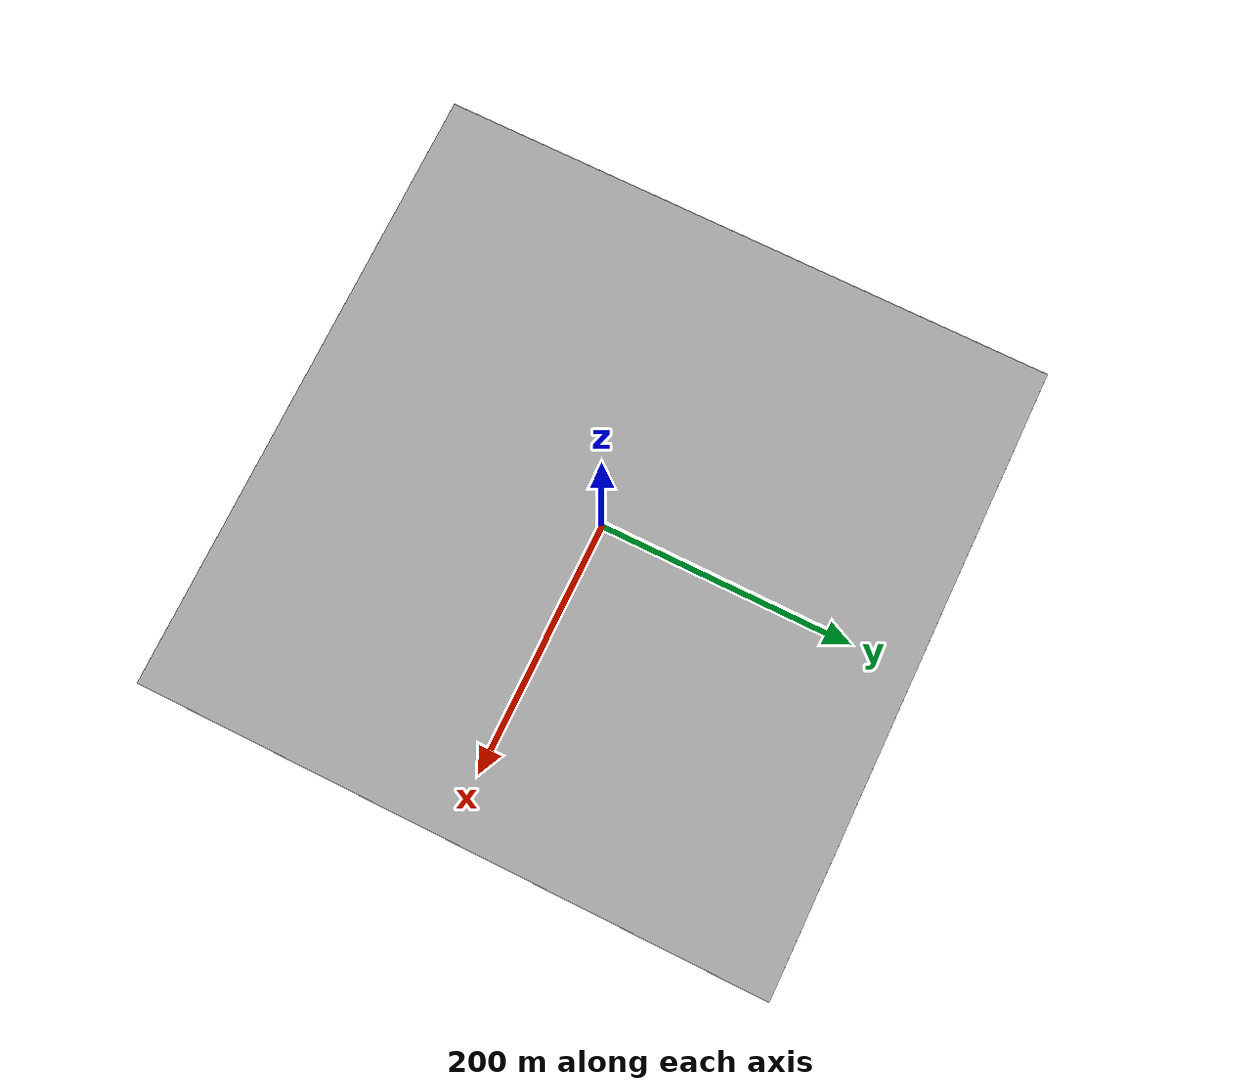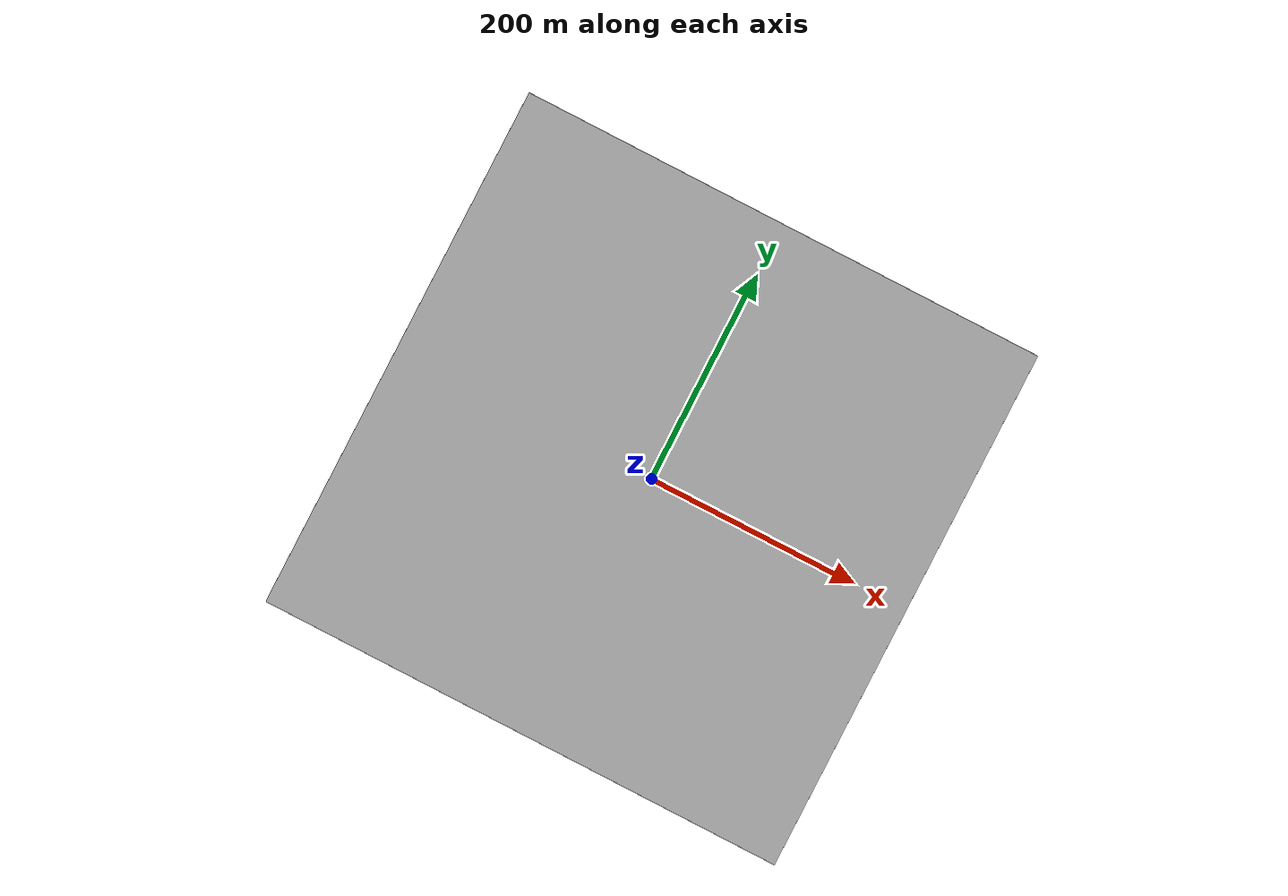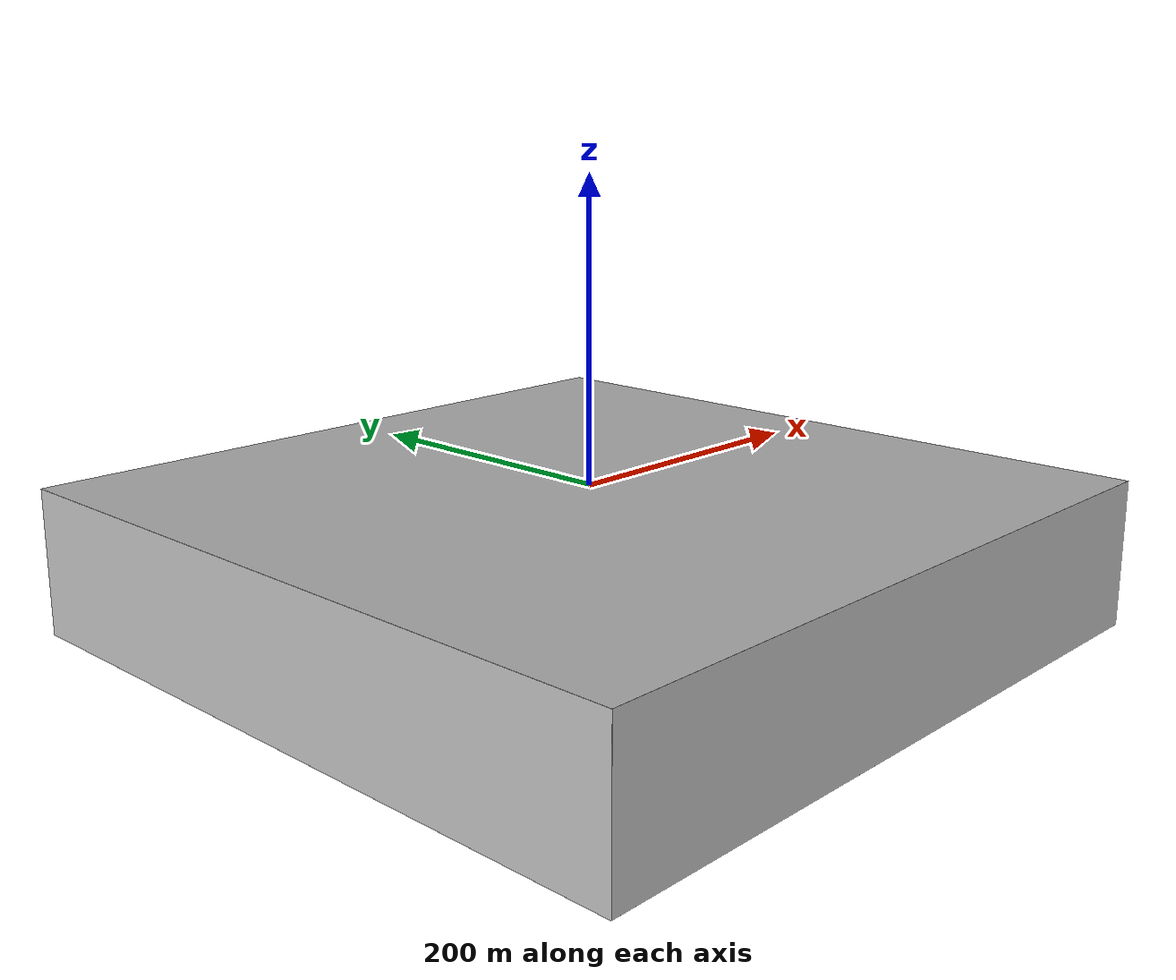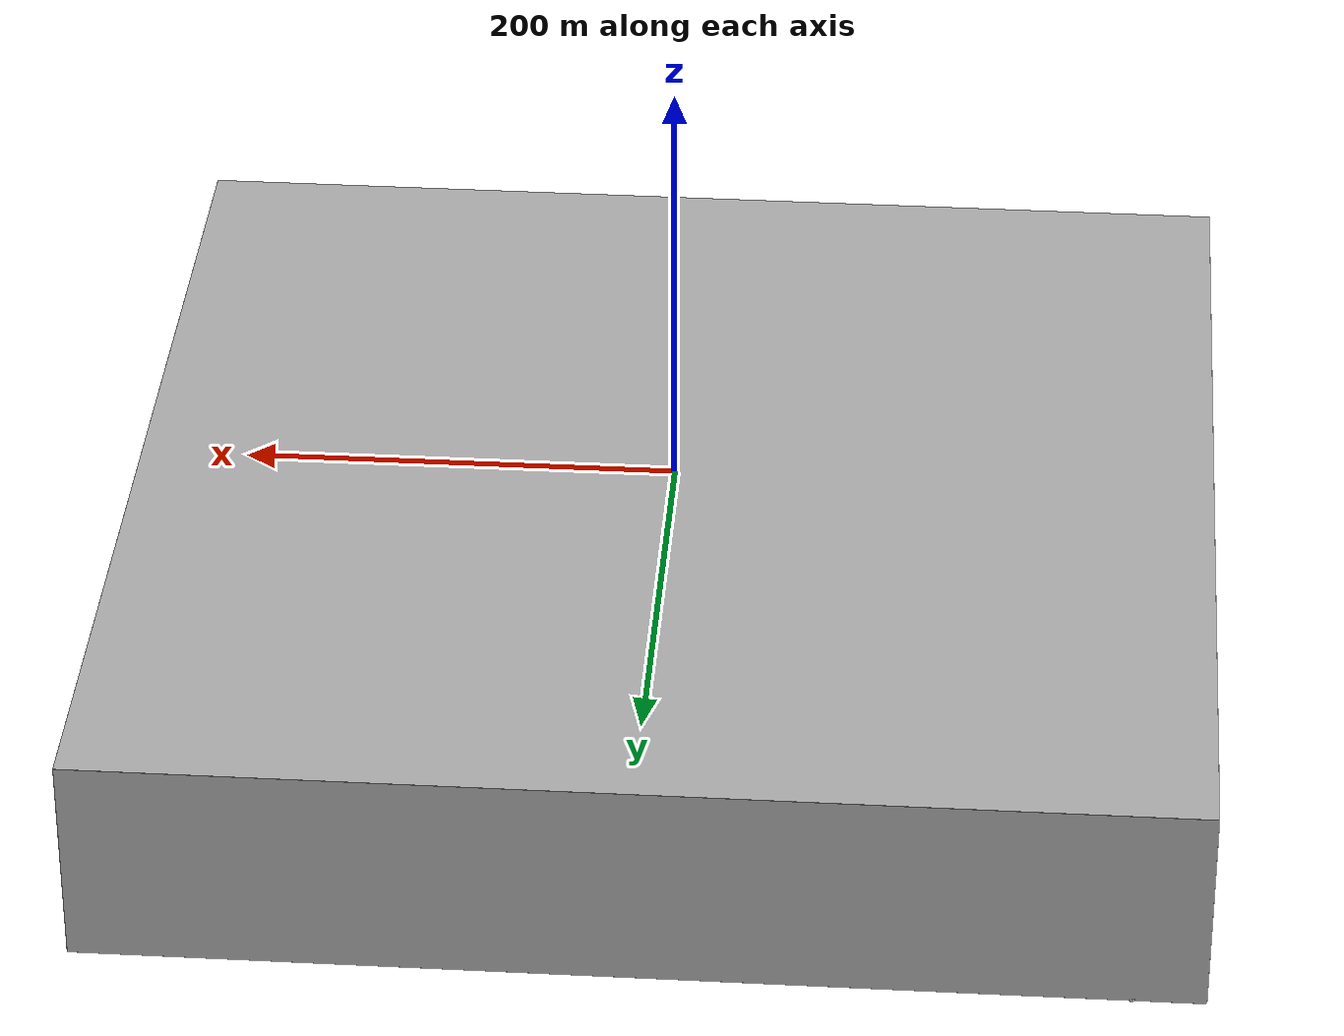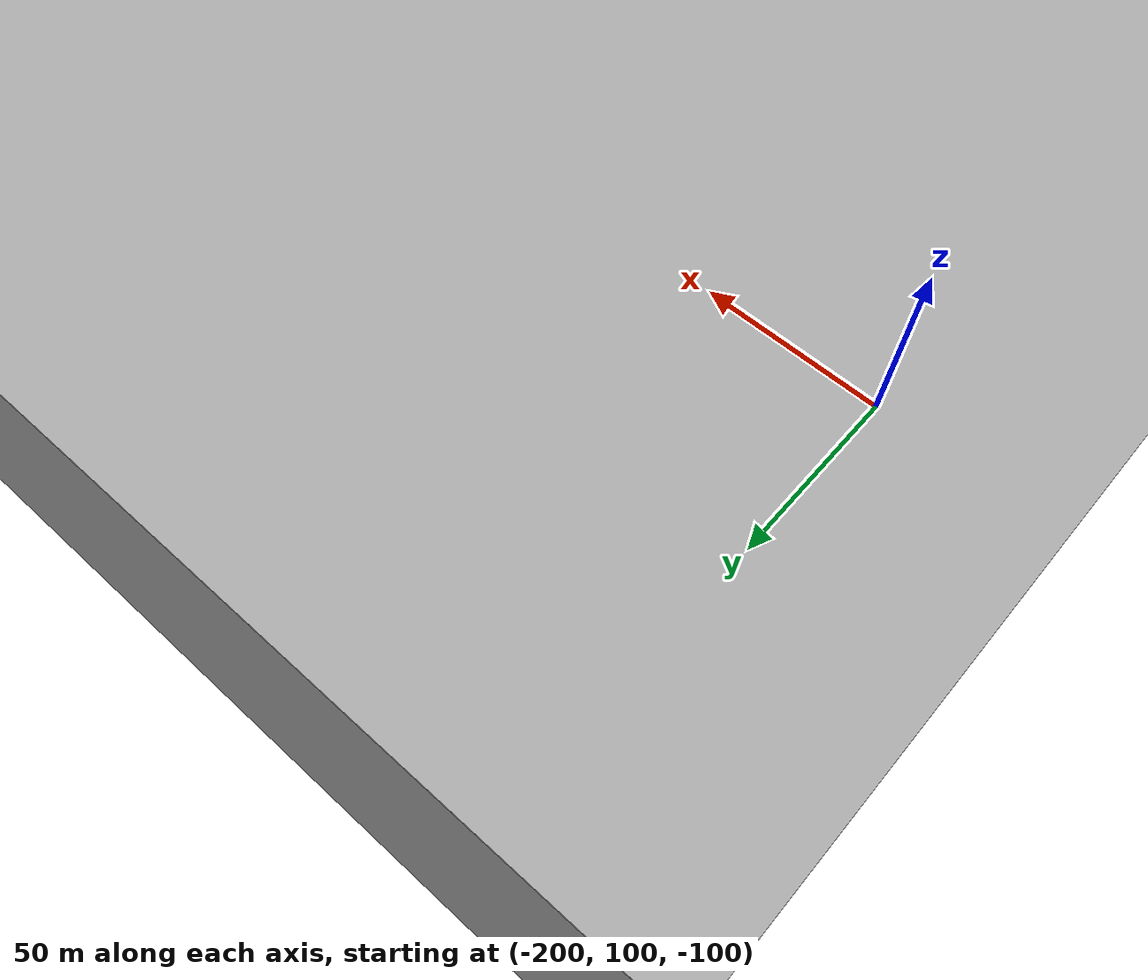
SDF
<sdf version="1.6">
 <world name="random_rocks">
  <physics name="default_physics" default="1" type="ode">
   <max_step_size>0.002</max_step_size>
   <real_time_factor>1</real_time_factor>
   <real_time_update_rate>500</real_time_update_rate>
   <ode>
    <solver>
     <type>quick</type>
     <iters>50</iters>
     <sor>0.5</sor>
     <use_dynamic_moi_rescaling>0</use_dynamic_moi_rescaling>
    </solver>
    <constraints>
     <cfm>0</cfm>
     <erp>0.2</erp>
     <contact_max_correcting_vel>100</contact_max_correcting_vel>
     <contact_surface_layer>0.001</contact_surface_layer>
    </constraints>
   </ode>
  </physics>
  <scene>
   <ambient>0.01 0.01 0.01 1</ambient>
   <sky><clouds><speed>12</speed></clouds></sky>
   <shadows>1</shadows>
   <fog>
    <color>0.1 0.2 0.3 1</color>
    <type>linear</type>
    <density>0.001</density>
    <start>10</start>
    <end>200</end>
   </fog>
   <background>0.7 0.7 0.7 1</background>
  </scene>
  <spherical_coordinates>
   <latitude_deg>56.719</latitude_deg>
   <longitude_deg>3.51562</longitude_deg>
   <surface_model>EARTH_WGS84</surface_model>
   <elevation>0</elevation>
   <heading_deg>0</heading_deg>
  </spherical_coordinates>
  <light name="sun" type="directional">
   <pose>0 0 10 0 -0 0</pose>
   <diffuse>0.8 0.8 0.8 1</diffuse>
   <specular>0.1 0.1 0.1 1</specular>
   <attenuation>
    <range>1000</range>
    <constant>0.9</constant>
    <linear>0.01</linear>
    <quadratic>0.001</quadratic>
   </attenuation>
   <direction>-0.5 0.5 -1</direction>
  </light>
  <model name="ned">
   <static>1</static>
   <link name="N">
    <gravity>0</gravity>
    <visual name="N_visual">
     <pose>0.25 0 0 3.14159 1.57079 3.14159</pose>
     <geometry><cylinder><radius>0.01</radius><length>0.5</length></cylinder></geometry>
     <material>
      <script><uri>file://media/materials/scripts/gazebo.material</uri><name>Gazebo/Red</name></script>
     </material>
    </visual>
   </link>
   <link name="E">
    <gravity>0</gravity>
    <pose>0 -0.25 0 1.5708 -0 0</pose>
    <visual name="E_visual">
     <geometry><cylinder><radius>0.01</radius><length>0.5</length></cylinder></geometry>
     <material>
      <script><uri>file://media/materials/scripts/gazebo.material</uri><name>Gazebo/Green</name></script>
     </material>
    </visual>
   </link>
   <link name="D">
    <gravity>0</gravity>
    <visual name="D_visual">
     <pose>0 0 -0.25 0 -0 0</pose>
     <geometry><cylinder><radius>0.01</radius><length>0.5</length></cylinder></geometry>
     <material>
      <script><uri>file://media/materials/scripts/gazebo.material</uri><name>Gazebo/Blue</name></script>
     </material>
    </visual>
   </link>
  </model>
  <model name="small_ocean_box">
   <static>1</static>
   <link name="link">
    <visual name="ground">
     <cast_shadows>0</cast_shadows>
     <pose>0 0 -100 0 -0 0</pose>
     <geometry><box><size>500 500 0.1</size></box></geometry>
     <material>
      <script>
       <uri>file://Media/materials/scripts/sand.material</uri>
       <name>UUVSimulator/SandAndStones</name>
      </script>
     </material>
     <laser_retro>50</laser_retro>
    </visual>
    <collision name="ground">
     <pose>0 0 -100 0 -0 0</pose>
     <geometry><box><size>500 500 0.1</size></box></geometry>
     <laser_retro>50</laser_retro>
    </collision>
    <visual name="surface">
     <cast_shadows>0</cast_shadows>
     <geometry><box><size>500 500 0.1</size></box></geometry>
     <material>
      <script>
       <uri>file://Media/materials/scripts/water.material</uri>
       <name>UUVSimulator/StaticDeepWater</name>
      </script>
     </material>
    </visual>
    <visual name="north">
     <cast_shadows>0</cast_shadows>
     <pose>250 0 -50 0 -0 0</pose>
     <geometry><box><size>0.1 500 100</size></box></geometry>
     <material>
      <script><uri>file://Media/materials/scripts/water.material</uri><name>UUVSimulator/SeaWall</name></script>
     </material>
    </visual>
    <visual name="south">
     <cast_shadows>0</cast_shadows>
     <pose>-250 0 -50 0 -0 0</pose>
     <geometry><box><size>0.1 500 100</size></box></geometry>
     <material>
      <script><uri>file://Media/materials/scripts/water.material</uri><name>UUVSimulator/SeaWall</name></script>
     </material>
    </visual>
    <visual name="east">
     <cast_shadows>0</cast_shadows>
     <pose>0 -250 -50 0 -0 0</pose>
     <geometry><box><size>500 0.1 100</size></box></geometry>
     <material>
      <script><uri>file://Media/materials/scripts/water.material</uri><name>UUVSimulator/SeaWall</name></script>
     </material>
    </visual>
    <visual name="west">
     <cast_shadows>0</cast_shadows>
     <pose>0 250 -50 0 -0 0</pose>
     <geometry><box><size>500 0.1 100</size></box></geometry>
     <material>
      <script><uri>file://Media/materials/scripts/water.material</uri><name>UUVSimulator/SeaWall</name></script>
     </material>
    </visual>
   </link>
  </model>
  <plugin name="underwater_world" filename="libuuv_underwater_world_ros_plugin.so">
   <namespace>hydrodynamics</namespace>
   <constant_current>
    <topic>current_velocity</topic>
    <velocity><mean>0</mean><min>-5</min><max>5</max><mu>0.0</mu><noiseAmp>0.0</noiseAmp></velocity>
    <horizontal_angle>
     <mean>0</mean>
     <min>-3.141592653589793238</min>
     <max>3.141592653589793238</max>
     <mu>0.0</mu>
     <noiseAmp>0.0</noiseAmp>
    </horizontal_angle>
    <vertical_angle>
     <mean>0</mean>
     <min>-3.141592653589793238</min>
     <max>3.141592653589793238</max>
     <mu>0.0</mu>
     <noiseAmp>0.0</noiseAmp>
    </vertical_angle>
   </constant_current>
  </plugin>
  <gravity>0 0 -9.8</gravity>
  <magnetic_field>6e-06 2.3e-05 -4.2e-05</magnetic_field>
  <atmosphere type="adiabatic"/>
  <model name="large_rock1_clone_0">
   <pose>38.0484 -60.4677 -99.9954 0 -0 0</pose>
   <static>1</static>
   <link name="large_rock::link">
    <collision name="large_rock_collision">
     <geometry>
      <mesh><uri>model://large_rock/meshes/large_rock_collision.stl</uri><scale>1 1 1</scale></mesh>
     </geometry>
     <laser_retro>200</laser_retro>
    </collision>
    <visual name="large_rock_visual">
     <geometry><mesh><uri>model://large_rock/meshes/large_rock.dae</uri><scale>1 1 1</scale></mesh></geometry>
     <laser_retro>200</laser_retro>
    </visual>
   </link>
  </model>
  <model name="large_rock1_clone_1">
   <pose>46.0885 183.863 -99.9551 0 -0 0</pose>
   <static>1</static>
   <link name="large_rock::link">
    <collision name="large_rock_collision">
     <geometry>
      <mesh><uri>model://large_rock/meshes/large_rock_collision.stl</uri><scale>1 1 1</scale></mesh>
     </geometry>
     <laser_retro>200</laser_retro>
    </collision>
    <visual name="large_rock_visual">
     <geometry><mesh><uri>model://large_rock/meshes/large_rock.dae</uri><scale>1 1 1</scale></mesh></geometry>
     <laser_retro>200</laser_retro>
    </visual>
   </link>
  </model>
  <model name="large_rock1_clone_2">
   <pose>-203.031 220.401 -99.9819 0 -0 0</pose>
   <static>1</static>
   <link name="large_rock::link">
    <collision name="large_rock_collision">
     <geometry>
      <mesh><uri>model://large_rock/meshes/large_rock_collision.stl</uri><scale>1 1 1</scale></mesh>
     </geometry>
     <laser_retro>200</laser_retro>
    </collision>
    <visual name="large_rock_visual">
     <geometry><mesh><uri>model://large_rock/meshes/large_rock.dae</uri><scale>1 1 1</scale></mesh></geometry>
     <laser_retro>200</laser_retro>
    </visual>
   </link>
  </model>
  <model name="large_rock1_clone_3">
   <pose>187.905 103.313 -100.019 0 -0 0</pose>
   <static>1</static>
   <link name="large_rock::link">
    <collision name="large_rock_collision">
     <geometry>
      <mesh><uri>model://large_rock/meshes/large_rock_collision.stl</uri><scale>1 1 1</scale></mesh>
     </geometry>
     <laser_retro>200</laser_retro>
    </collision>
    <visual name="large_rock_visual">
     <geometry><mesh><uri>model://large_rock/meshes/large_rock.dae</uri><scale>1 1 1</scale></mesh></geometry>
     <laser_retro>200</laser_retro>
    </visual>
   </link>
  </model>
  <model name="large_rock1_clone_4">
   <pose>-201.431 -118.857 -100.018 0 -0 0</pose>
   <static>1</static>
   <link name="large_rock::link">
    <collision name="large_rock_collision">
     <geometry>
      <mesh><uri>model://large_rock/meshes/large_rock_collision.stl</uri><scale>1 1 1</scale></mesh>
     </geometry>
     <laser_retro>200</laser_retro>
    </collision>
    <visual name="large_rock_visual">
     <geometry><mesh><uri>model://large_rock/meshes/large_rock.dae</uri><scale>1 1 1</scale></mesh></geometry>
     <laser_retro>200</laser_retro>
    </visual>
   </link>
  </model>
  <model name="large_rock1_clone_5">
   <pose>174.909 -203.526 -99.9901 0 -0 0</pose>
   <static>1</static>
   <link name="large_rock::link">
    <collision name="large_rock_collision">
     <geometry>
      <mesh><uri>model://large_rock/meshes/large_rock_collision.stl</uri><scale>1 1 1</scale></mesh>
     </geometry>
     <laser_retro>200</laser_retro>
    </collision>
    <visual name="large_rock_visual">
     <geometry><mesh><uri>model://large_rock/meshes/large_rock.dae</uri><scale>1 1 1</scale></mesh></geometry>
     <laser_retro>200</laser_retro>
    </visual>
   </link>
  </model>
  <model name="large_rock1_clone_6">
   <pose>-55.0703 91.406 -99.9714 0 -0 0</pose>
   <static>1</static>
   <link name="large_rock::link">
    <collision name="large_rock_collision">
     <geometry>
      <mesh><uri>model://large_rock/meshes/large_rock_collision.stl</uri><scale>1 1 1</scale></mesh>
     </geometry>
     <laser_retro>200</laser_retro>
    </collision>
    <visual name="large_rock_visual">
     <geometry><mesh><uri>model://large_rock/meshes/large_rock.dae</uri><scale>1 1 1</scale></mesh></geometry>
     <laser_retro>200</laser_retro>
    </visual>
   </link>
  </model>
  <model name="large_rock1_clone_7">
   <pose>-111.911 227.216 -100.014 0 -0 0</pose>
   <static>1</static>
   <link name="large_rock::link">
    <collision name="large_rock_collision">
     <geometry>
      <mesh><uri>model://large_rock/meshes/large_rock_collision.stl</uri><scale>1 1 1</scale></mesh>
     </geometry>
     <laser_retro>200</laser_retro>
    </collision>
    <visual name="large_rock_visual">
     <geometry><mesh><uri>model://large_rock/meshes/large_rock.dae</uri><scale>1 1 1</scale></mesh></geometry>
     <laser_retro>200</laser_retro>
    </visual>
   </link>
  </model>
  <model name="large_rock1_clone_8">
   <pose>-214.552 234.636 -100.041 0 -0 0</pose>
   <static>1</static>
   <link name="large_rock::link">
    <collision name="large_rock_collision">
     <geometry>
      <mesh><uri>model://large_rock/meshes/large_rock_collision.stl</uri><scale>1 1 1</scale></mesh>
     </geometry>
     <laser_retro>200</laser_retro>
    </collision>
    <visual name="large_rock_visual">
     <geometry><mesh><uri>model://large_rock/meshes/large_rock.dae</uri><scale>1 1 1</scale></mesh></geometry>
     <laser_retro>200</laser_retro>
    </visual>
   </link>
  </model>
  <model name="large_rock1_clone_9">
   <pose>130.582 -157.1 -100.011 0 -0 0</pose>
   <static>1</static>
   <link name="large_rock::link">
    <collision name="large_rock_collision">
     <geometry>
      <mesh><uri>model://large_rock/meshes/large_rock_collision.stl</uri><scale>1 1 1</scale></mesh>
     </geometry>
     <laser_retro>200</laser_retro>
    </collision>
    <visual name="large_rock_visual">
     <geometry><mesh><uri>model://large_rock/meshes/large_rock.dae</uri><scale>1 1 1</scale></mesh></geometry>
     <laser_retro>200</laser_retro>
    </visual>
   </link>
  </model>
  <model name="large_rock1_clone_10">
   <pose>41.7395 -59.7861 -99.9639 0 -0 0</pose>
   <static>1</static>
   <link name="large_rock::link">
    <collision name="large_rock_collision">
     <geometry>
      <mesh><uri>model://large_rock/meshes/large_rock_collision.stl</uri><scale>1 1 1</scale></mesh>
     </geometry>
     <laser_retro>200</laser_retro>
    </collision>
    <visual name="large_rock_visual">
     <geometry><mesh><uri>model://large_rock/meshes/large_rock.dae</uri><scale>1 1 1</scale></mesh></geometry>
     <laser_retro>200</laser_retro>
    </visual>
   </link>
  </model>
  <model name="large_rock1_clone_11">
   <pose>-203.16 185.298 -100.036 0 -0 0</pose>
   <static>1</static>
   <link name="large_rock::link">
    <collision name="large_rock_collision">
     <geometry>
      <mesh><uri>model://large_rock/meshes/large_rock_collision.stl</uri><scale>1 1 1</scale></mesh>
     </geometry>
     <laser_retro>200</laser_retro>
    </collision>
    <visual name="large_rock_visual">
     <geometry><mesh><uri>model://large_rock/meshes/large_rock.dae</uri><scale>1 1 1</scale></mesh></geometry>
     <laser_retro>200</laser_retro>
    </visual>
   </link>
  </model>
  <model name="large_rock1_clone_12">
   <pose>53.4693 -113.467 -100.012 0 -0 0</pose>
   <static>1</static>
   <link name="large_rock::link">
    <collision name="large_rock_collision">
     <geometry>
      <mesh><uri>model://large_rock/meshes/large_rock_collision.stl</uri><scale>1 1 1</scale></mesh>
     </geometry>
     <laser_retro>200</laser_retro>
    </collision>
    <visual name="large_rock_visual">
     <geometry><mesh><uri>model://large_rock/meshes/large_rock.dae</uri><scale>1 1 1</scale></mesh></geometry>
     <laser_retro>200</laser_retro>
    </visual>
   </link>
  </model>
  <model name="large_rock1_clone_13">
   <pose>-36.726 -65.6015 -99.9737 0 -0 0</pose>
   <static>1</static>
   <link name="large_rock::link">
    <collision name="large_rock_collision">
     <geometry>
      <mesh><uri>model://large_rock/meshes/large_rock_collision.stl</uri><scale>1 1 1</scale></mesh>
     </geometry>
     <laser_retro>200</laser_retro>
    </collision>
    <visual name="large_rock_visual">
     <geometry><mesh><uri>model://large_rock/meshes/large_rock.dae</uri><scale>1 1 1</scale></mesh></geometry>
     <laser_retro>200</laser_retro>
    </visual>
   </link>
  </model>
  <model name="large_rock1_clone_14">
   <pose>12.1855 221.851 -100.026 0 -0 0</pose>
   <static>1</static>
   <link name="large_rock::link">
    <collision name="large_rock_collision">
     <geometry>
      <mesh><uri>model://large_rock/meshes/large_rock_collision.stl</uri><scale>1 1 1</scale></mesh>
     </geometry>
     <laser_retro>200</laser_retro>
    </collision>
    <visual name="large_rock_visual">
     <geometry><mesh><uri>model://large_rock/meshes/large_rock.dae</uri><scale>1 1 1</scale></mesh></geometry>
     <laser_retro>200</laser_retro>
    </visual>
   </link>
  </model>
  <model name="large_rock1_clone_15">
   <pose>189.906 61.0531 -100.011 0 -0 0</pose>
   <static>1</static>
   <link name="large_rock::link">
    <collision name="large_rock_collision">
     <geometry>
      <mesh><uri>model://large_rock/meshes/large_rock_collision.stl</uri><scale>1 1 1</scale></mesh>
     </geometry>
     <laser_retro>200</laser_retro>
    </collision>
    <visual name="large_rock_visual">
     <geometry><mesh><uri>model://large_rock/meshes/large_rock.dae</uri><scale>1 1 1</scale></mesh></geometry>
     <laser_retro>200</laser_retro>
    </visual>
   </link>
  </model>
  <model name="large_rock1_clone_16">
   <pose>-246.274 42.0096 -100.001 0 -0 0</pose>
   <static>1</static>
   <link name="large_rock::link">
    <collision name="large_rock_collision">
     <geometry>
      <mesh><uri>model://large_rock/meshes/large_rock_collision.stl</uri><scale>1 1 1</scale></mesh>
     </geometry>
     <laser_retro>200</laser_retro>
    </collision>
    <visual name="large_rock_visual">
     <geometry><mesh><uri>model://large_rock/meshes/large_rock.dae</uri><scale>1 1 1</scale></mesh></geometry>
     <laser_retro>200</laser_retro>
    </visual>
   </link>
  </model>
  <model name="large_rock1_clone_17">
   <pose>38.1481 84.3567 -99.9553 0 -0 0</pose>
   <static>1</static>
   <link name="large_rock::link">
    <collision name="large_rock_collision">
     <geometry>
      <mesh><uri>model://large_rock/meshes/large_rock_collision.stl</uri><scale>1 1 1</scale></mesh>
     </geometry>
     <laser_retro>200</laser_retro>
    </collision>
    <visual name="large_rock_visual">
     <geometry><mesh><uri>model://large_rock/meshes/large_rock.dae</uri><scale>1 1 1</scale></mesh></geometry>
     <laser_retro>200</laser_retro>
    </visual>
   </link>
  </model>
  <model name="large_rock1_clone_18">
   <pose>-246.398 111.463 -99.9992 0 -0 0</pose>
   <static>1</static>
   <link name="large_rock::link">
    <collision name="large_rock_collision">
     <geometry>
      <mesh><uri>model://large_rock/meshes/large_rock_collision.stl</uri><scale>1 1 1</scale></mesh>
     </geometry>
     <laser_retro>200</laser_retro>
    </collision>
    <visual name="large_rock_visual">
     <geometry><mesh><uri>model://large_rock/meshes/large_rock.dae</uri><scale>1 1 1</scale></mesh></geometry>
     <laser_retro>200</laser_retro>
    </visual>
   </link>
  </model>
  <model name="large_rock1_clone_19">
   <pose>-170.704 -124.144 -99.9811 0 -0 0</pose>
   <static>1</static>
   <link name="large_rock::link">
    <collision name="large_rock_collision">
     <geometry>
      <mesh><uri>model://large_rock/meshes/large_rock_collision.stl</uri><scale>1 1 1</scale></mesh>
     </geometry>
     <laser_retro>200</laser_retro>
    </collision>
    <visual name="large_rock_visual">
     <geometry><mesh><uri>model://large_rock/meshes/large_rock.dae</uri><scale>1 1 1</scale></mesh></geometry>
     <laser_retro>200</laser_retro>
    </visual>
   </link>
  </model>
  <model name="large_rock1_clone_20">
   <pose>-127 -194.303 -100.044 0 -0 0</pose>
   <static>1</static>
   <link name="large_rock::link">
    <collision name="large_rock_collision">
     <geometry>
      <mesh><uri>model://large_rock/meshes/large_rock_collision.stl</uri><scale>1 1 1</scale></mesh>
     </geometry>
     <laser_retro>200</laser_retro>
    </collision>
    <visual name="large_rock_visual">
     <geometry><mesh><uri>model://large_rock/meshes/large_rock.dae</uri><scale>1 1 1</scale></mesh></geometry>
     <laser_retro>200</laser_retro>
    </visual>
   </link>
  </model>
  <model name="large_rock1_clone_21">
   <pose>-32.4392 -12.8952 -100.037 0 -0 0</pose>
   <static>1</static>
   <link name="large_rock::link">
    <collision name="large_rock_collision">
     <geometry>
      <mesh><uri>model://large_rock/meshes/large_rock_collision.stl</uri><scale>1 1 1</scale></mesh>
     </geometry>
     <laser_retro>200</laser_retro>
    </collision>
    <visual name="large_rock_visual">
     <geometry><mesh><uri>model://large_rock/meshes/large_rock.dae</uri><scale>1 1 1</scale></mesh></geometry>
     <laser_retro>200</laser_retro>
    </visual>
   </link>
  </model>
  <model name="large_rock1_clone_22">
   <pose>27.8997 151.037 -100.035 0 -0 0</pose>
   <static>1</static>
   <link name="large_rock::link">
    <collision name="large_rock_collision">
     <geometry>
      <mesh><uri>model://large_rock/meshes/large_rock_collision.stl</uri><scale>1 1 1</scale></mesh>
     </geometry>
     <laser_retro>200</laser_retro>
    </collision>
    <visual name="large_rock_visual">
     <geometry><mesh><uri>model://large_rock/meshes/large_rock.dae</uri><scale>1 1 1</scale></mesh></geometry>
     <laser_retro>200</laser_retro>
    </visual>
   </link>
  </model>
  <model name="large_rock1_clone_23">
   <pose>-21.9768 -170.254 -100.044 0 -0 0</pose>
   <static>1</static>
   <link name="large_rock::link">
    <collision name="large_rock_collision">
     <geometry>
      <mesh><uri>model://large_rock/meshes/large_rock_collision.stl</uri><scale>1 1 1</scale></mesh>
     </geometry>
     <laser_retro>200</laser_retro>
    </collision>
    <visual name="large_rock_visual">
     <geometry><mesh><uri>model://large_rock/meshes/large_rock.dae</uri><scale>1 1 1</scale></mesh></geometry>
     <laser_retro>200</laser_retro>
    </visual>
   </link>
  </model>
  <model name="large_rock1_clone_24">
   <pose>200.262 -98.5392 -100 0 -0 0</pose>
   <static>1</static>
   <link name="large_rock::link">
    <collision name="large_rock_collision">
     <geometry>
      <mesh><uri>model://large_rock/meshes/large_rock_collision.stl</uri><scale>1 1 1</scale></mesh>
     </geometry>
     <laser_retro>200</laser_retro>
    </collision>
    <visual name="large_rock_visual">
     <geometry><mesh><uri>model://large_rock/meshes/large_rock.dae</uri><scale>1 1 1</scale></mesh></geometry>
     <laser_retro>200</laser_retro>
    </visual>
   </link>
  </model>
  <model name="large_rock1_clone_25">
   <pose>-89.034 -22.2824 -99.9756 0 -0 0</pose>
   <static>1</static>
   <link name="large_rock::link">
    <collision name="large_rock_collision">
     <geometry>
      <mesh><uri>model://large_rock/meshes/large_rock_collision.stl</uri><scale>1 1 1</scale></mesh>
     </geometry>
     <laser_retro>200</laser_retro>
    </collision>
    <visual name="large_rock_visual">
     <geometry><mesh><uri>model://large_rock/meshes/large_rock.dae</uri><scale>1 1 1</scale></mesh></geometry>
     <laser_retro>200</laser_retro>
    </visual>
   </link>
  </model>
  <model name="large_rock1_clone_26">
   <pose>-108.142 -124.052 -99.9551 0 -0 0</pose>
   <static>1</static>
   <link name="large_rock::link">
    <collision name="large_rock_collision">
     <geometry>
      <mesh><uri>model://large_rock/meshes/large_rock_collision.stl</uri><scale>1 1 1</scale></mesh>
     </geometry>
     <laser_retro>200</laser_retro>
    </collision>
    <visual name="large_rock_visual">
     <geometry><mesh><uri>model://large_rock/meshes/large_rock.dae</uri><scale>1 1 1</scale></mesh></geometry>
     <laser_retro>200</laser_retro>
    </visual>
   </link>
  </model>
  <model name="large_rock1_clone_27">
   <pose>56.5143 209.307 -100 0 -0 0</pose>
   <static>1</static>
   <link name="large_rock::link">
    <collision name="large_rock_collision">
     <geometry>
      <mesh><uri>model://large_rock/meshes/large_rock_collision.stl</uri><scale>1 1 1</scale></mesh>
     </geometry>
     <laser_retro>200</laser_retro>
    </collision>
    <visual name="large_rock_visual">
     <geometry><mesh><uri>model://large_rock/meshes/large_rock.dae</uri><scale>1 1 1</scale></mesh></geometry>
     <laser_retro>200</laser_retro>
    </visual>
   </link>
  </model>
  <model name="large_rock1_clone_28">
   <pose>241.413 206.534 -99.9809 0 -0 0</pose>
   <static>1</static>
   <link name="large_rock::link">
    <collision name="large_rock_collision">
     <geometry>
      <mesh><uri>model://large_rock/meshes/large_rock_collision.stl</uri><scale>1 1 1</scale></mesh>
     </geometry>
     <laser_retro>200</laser_retro>
    </collision>
    <visual name="large_rock_visual">
     <geometry><mesh><uri>model://large_rock/meshes/large_rock.dae</uri><scale>1 1 1</scale></mesh></geometry>
     <laser_retro>200</laser_retro>
    </visual>
   </link>
  </model>
  <model name="large_rock1_clone_29">
   <pose>-0.756909 174.87 -99.9763 0 -0 0</pose>
   <static>1</static>
   <link name="large_rock::link">
    <collision name="large_rock_collision">
     <geometry>
      <mesh><uri>model://large_rock/meshes/large_rock_collision.stl</uri><scale>1 1 1</scale></mesh>
     </geometry>
     <laser_retro>200</laser_retro>
    </collision>
    <visual name="large_rock_visual">
     <geometry><mesh><uri>model://large_rock/meshes/large_rock.dae</uri><scale>1 1 1</scale></mesh></geometry>
     <laser_retro>200</laser_retro>
    </visual>
   </link>
  </model>
  <model name="large_rock1_clone_30">
   <pose>166.973 0.073289 -99.9931 0 -0 0</pose>
   <static>1</static>
   <link name="large_rock::link">
    <collision name="large_rock_collision">
     <geometry>
      <mesh><uri>model://large_rock/meshes/large_rock_collision.stl</uri><scale>1 1 1</scale></mesh>
     </geometry>
     <laser_retro>200</laser_retro>
    </collision>
    <visual name="large_rock_visual">
     <geometry><mesh><uri>model://large_rock/meshes/large_rock.dae</uri><scale>1 1 1</scale></mesh></geometry>
     <laser_retro>200</laser_retro>
    </visual>
   </link>
  </model>
  <model name="large_rock1_clone_31">
   <pose>-187.361 -207.237 -99.9547 0 -0 0</pose>
   <static>1</static>
   <link name="large_rock::link">
    <collision name="large_rock_collision">
     <geometry>
      <mesh><uri>model://large_rock/meshes/large_rock_collision.stl</uri><scale>1 1 1</scale></mesh>
     </geometry>
     <laser_retro>200</laser_retro>
    </collision>
    <visual name="large_rock_visual">
     <geometry><mesh><uri>model://large_rock/meshes/large_rock.dae</uri><scale>1 1 1</scale></mesh></geometry>
     <laser_retro>200</laser_retro>
    </visual>
   </link>
  </model>
  <model name="large_rock1_clone_32">
   <pose>-104.811 -66.9233 -99.9893 0 -0 0</pose>
   <static>1</static>
   <link name="large_rock::link">
    <collision name="large_rock_collision">
     <geometry>
      <mesh><uri>model://large_rock/meshes/large_rock_collision.stl</uri><scale>1 1 1</scale></mesh>
     </geometry>
     <laser_retro>200</laser_retro>
    </collision>
    <visual name="large_rock_visual">
     <geometry><mesh><uri>model://large_rock/meshes/large_rock.dae</uri><scale>1 1 1</scale></mesh></geometry>
     <laser_retro>200</laser_retro>
    </visual>
   </link>
  </model>
  <model name="large_rock1_clone_33">
   <pose>231.909 -126.423 -99.9935 0 -0 0</pose>
   <static>1</static>
   <link name="large_rock::link">
    <collision name="large_rock_collision">
     <geometry>
      <mesh><uri>model://large_rock/meshes/large_rock_collision.stl</uri><scale>1 1 1</scale></mesh>
     </geometry>
     <laser_retro>200</laser_retro>
    </collision>
    <visual name="large_rock_visual">
     <geometry><mesh><uri>model://large_rock/meshes/large_rock.dae</uri><scale>1 1 1</scale></mesh></geometry>
     <laser_retro>200</laser_retro>
    </visual>
   </link>
  </model>
  <model name="large_rock1_clone_34">
   <pose>-111.113 -132.344 -99.9882 0 -0 0</pose>
   <static>1</static>
   <link name="large_rock::link">
    <collision name="large_rock_collision">
     <geometry>
      <mesh><uri>model://large_rock/meshes/large_rock_collision.stl</uri><scale>1 1 1</scale></mesh>
     </geometry>
     <laser_retro>200</laser_retro>
    </collision>
    <visual name="large_rock_visual">
     <geometry><mesh><uri>model://large_rock/meshes/large_rock.dae</uri><scale>1 1 1</scale></mesh></geometry>
     <laser_retro>200</laser_retro>
    </visual>
   </link>
  </model>
  <model name="large_rock1_clone_35">
   <pose>-110.121 4.53843 -99.9509 0 -0 0</pose>
   <static>1</static>
   <link name="large_rock::link">
    <collision name="large_rock_collision">
     <geometry>
      <mesh><uri>model://large_rock/meshes/large_rock_collision.stl</uri><scale>1 1 1</scale></mesh>
     </geometry>
     <laser_retro>200</laser_retro>
    </collision>
    <visual name="large_rock_visual">
     <geometry><mesh><uri>model://large_rock/meshes/large_rock.dae</uri><scale>1 1 1</scale></mesh></geometry>
     <laser_retro>200</laser_retro>
    </visual>
   </link>
  </model>
  <model name="large_rock1_clone_36">
   <pose>-48.7905 53.9447 -99.9859 0 -0 0</pose>
   <static>1</static>
   <link name="large_rock::link">
    <collision name="large_rock_collision">
     <geometry>
      <mesh><uri>model://large_rock/meshes/large_rock_collision.stl</uri><scale>1 1 1</scale></mesh>
     </geometry>
     <laser_retro>200</laser_retro>
    </collision>
    <visual name="large_rock_visual">
     <geometry><mesh><uri>model://large_rock/meshes/large_rock.dae</uri><scale>1 1 1</scale></mesh></geometry>
     <laser_retro>200</laser_retro>
    </visual>
   </link>
  </model>
  <model name="large_rock1_clone_37">
   <pose>9.30718 190.545 -100.005 0 -0 0</pose>
   <static>1</static>
   <link name="large_rock::link">
    <collision name="large_rock_collision">
     <geometry>
      <mesh><uri>model://large_rock/meshes/large_rock_collision.stl</uri><scale>1 1 1</scale></mesh>
     </geometry>
     <laser_retro>200</laser_retro>
    </collision>
    <visual name="large_rock_visual">
     <geometry><mesh><uri>model://large_rock/meshes/large_rock.dae</uri><scale>1 1 1</scale></mesh></geometry>
     <laser_retro>200</laser_retro>
    </visual>
   </link>
  </model>
  <model name="large_rock1_clone_38">
   <pose>145.81 -124.642 -99.9714 0 -0 0</pose>
   <static>1</static>
   <link name="large_rock::link">
    <collision name="large_rock_collision">
     <geometry>
      <mesh><uri>model://large_rock/meshes/large_rock_collision.stl</uri><scale>1 1 1</scale></mesh>
     </geometry>
     <laser_retro>200</laser_retro>
    </collision>
    <visual name="large_rock_visual">
     <geometry><mesh><uri>model://large_rock/meshes/large_rock.dae</uri><scale>1 1 1</scale></mesh></geometry>
     <laser_retro>200</laser_retro>
    </visual>
   </link>
  </model>
  <model name="large_rock1_clone_39">
   <pose>81.4187 60.4096 -99.9693 0 -0 0</pose>
   <static>1</static>
   <link name="large_rock::link">
    <collision name="large_rock_collision">
     <geometry>
      <mesh><uri>model://large_rock/meshes/large_rock_collision.stl</uri><scale>1 1 1</scale></mesh>
     </geometry>
     <laser_retro>200</laser_retro>
    </collision>
    <visual name="large_rock_visual">
     <geometry><mesh><uri>model://large_rock/meshes/large_rock.dae</uri><scale>1 1 1</scale></mesh></geometry>
     <laser_retro>200</laser_retro>
    </visual>
   </link>
  </model>
  <model name="large_rock1_clone_40">
   <pose>3.80745 -160.986 -100.013 0 -0 0</pose>
   <static>1</static>
   <link name="large_rock::link">
    <collision name="large_rock_collision">
     <geometry>
      <mesh><uri>model://large_rock/meshes/large_rock_collision.stl</uri><scale>1 1 1</scale></mesh>
     </geometry>
     <laser_retro>200</laser_retro>
    </collision>
    <visual name="large_rock_visual">
     <geometry><mesh><uri>model://large_rock/meshes/large_rock.dae</uri><scale>1 1 1</scale></mesh></geometry>
     <laser_retro>200</laser_retro>
    </visual>
   </link>
  </model>
  <model name="large_rock1_clone_41">
   <pose>71.9819 -12.7857 -100.047 0 -0 0</pose>
   <static>1</static>
   <link name="large_rock::link">
    <collision name="large_rock_collision">
     <geometry>
      <mesh><uri>model://large_rock/meshes/large_rock_collision.stl</uri><scale>1 1 1</scale></mesh>
     </geometry>
     <laser_retro>200</laser_retro>
    </collision>
    <visual name="large_rock_visual">
     <geometry><mesh><uri>model://large_rock/meshes/large_rock.dae</uri><scale>1 1 1</scale></mesh></geometry>
     <laser_retro>200</laser_retro>
    </visual>
   </link>
  </model>
  <model name="large_rock1_clone_42">
   <pose>-164.775 -184.313 -100.015 0 -0 0</pose>
   <static>1</static>
   <link name="large_rock::link">
    <collision name="large_rock_collision">
     <geometry>
      <mesh><uri>model://large_rock/meshes/large_rock_collision.stl</uri><scale>1 1 1</scale></mesh>
     </geometry>
     <laser_retro>200</laser_retro>
    </collision>
    <visual name="large_rock_visual">
     <geometry><mesh><uri>model://large_rock/meshes/large_rock.dae</uri><scale>1 1 1</scale></mesh></geometry>
     <laser_retro>200</laser_retro>
    </visual>
   </link>
  </model>
  <model name="large_rock1_clone_43">
   <pose>-204.154 -163.977 -100.034 0 -0 0</pose>
   <static>1</static>
   <link name="large_rock::link">
    <collision name="large_rock_collision">
     <geometry>
      <mesh><uri>model://large_rock/meshes/large_rock_collision.stl</uri><scale>1 1 1</scale></mesh>
     </geometry>
     <laser_retro>200</laser_retro>
    </collision>
    <visual name="large_rock_visual">
     <geometry><mesh><uri>model://large_rock/meshes/large_rock.dae</uri><scale>1 1 1</scale></mesh></geometry>
     <laser_retro>200</laser_retro>
    </visual>
   </link>
  </model>
  <model name="large_rock1_clone_44">
   <pose>203.819 -246.538 -100.038 0 -0 0</pose>
   <static>1</static>
   <link name="large_rock::link">
    <collision name="large_rock_collision">
     <geometry>
      <mesh><uri>model://large_rock/meshes/large_rock_collision.stl</uri><scale>1 1 1</scale></mesh>
     </geometry>
     <laser_retro>200</laser_retro>
    </collision>
    <visual name="large_rock_visual">
     <geometry><mesh><uri>model://large_rock/meshes/large_rock.dae</uri><scale>1 1 1</scale></mesh></geometry>
     <laser_retro>200</laser_retro>
    </visual>
   </link>
  </model>
  <model name="large_rock1_clone_45">
   <pose>-115.157 128.675 -99.9629 0 -0 0</pose>
   <static>1</static>
   <link name="large_rock::link">
    <collision name="large_rock_collision">
     <geometry>
      <mesh><uri>model://large_rock/meshes/large_rock_collision.stl</uri><scale>1 1 1</scale></mesh>
     </geometry>
     <laser_retro>200</laser_retro>
    </collision>
    <visual name="large_rock_visual">
     <geometry><mesh><uri>model://large_rock/meshes/large_rock.dae</uri><scale>1 1 1</scale></mesh></geometry>
     <laser_retro>200</laser_retro>
    </visual>
   </link>
  </model>
  <model name="large_rock1_clone_46">
   <pose>161.109 -106.427 -100.028 0 -0 0</pose>
   <static>1</static>
   <link name="large_rock::link">
    <collision name="large_rock_collision">
     <geometry>
      <mesh><uri>model://large_rock/meshes/large_rock_collision.stl</uri><scale>1 1 1</scale></mesh>
     </geometry>
     <laser_retro>200</laser_retro>
    </collision>
    <visual name="large_rock_visual">
     <geometry><mesh><uri>model://large_rock/meshes/large_rock.dae</uri><scale>1 1 1</scale></mesh></geometry>
     <laser_retro>200</laser_retro>
    </visual>
   </link>
  </model>
  <model name="large_rock1_clone_47">
   <pose>34.4772 -4.30729 -100.04 0 -0 0</pose>
   <static>1</static>
   <link name="large_rock::link">
    <collision name="large_rock_collision">
     <geometry>
      <mesh><uri>model://large_rock/meshes/large_rock_collision.stl</uri><scale>1 1 1</scale></mesh>
     </geometry>
     <laser_retro>200</laser_retro>
    </collision>
    <visual name="large_rock_visual">
     <geometry><mesh><uri>model://large_rock/meshes/large_rock.dae</uri><scale>1 1 1</scale></mesh></geometry>
     <laser_retro>200</laser_retro>
    </visual>
   </link>
  </model>
  <model name="large_rock1_clone_48">
   <pose>-38.195 14.52 -99.9733 0 -0 0</pose>
   <static>1</static>
   <link name="large_rock::link">
    <collision name="large_rock_collision">
     <geometry>
      <mesh><uri>model://large_rock/meshes/large_rock_collision.stl</uri><scale>1 1 1</scale></mesh>
     </geometry>
     <laser_retro>200</laser_retro>
    </collision>
    <visual name="large_rock_visual">
     <geometry><mesh><uri>model://large_rock/meshes/large_rock.dae</uri><scale>1 1 1</scale></mesh></geometry>
     <laser_retro>200</laser_retro>
    </visual>
   </link>
  </model>
  <model name="large_rock1_clone_49">
   <pose>-167.565 57.3315 -100.013 0 -0 0</pose>
   <static>1</static>
   <link name="large_rock::link">
    <collision name="large_rock_collision">
     <geometry>
      <mesh><uri>model://large_rock/meshes/large_rock_collision.stl</uri><scale>1 1 1</scale></mesh>
     </geometry>
     <laser_retro>200</laser_retro>
    </collision>
    <visual name="large_rock_visual">
     <geometry><mesh><uri>model://large_rock/meshes/large_rock.dae</uri><scale>1 1 1</scale></mesh></geometry>
     <laser_retro>200</laser_retro>
    </visual>
   </link>
  </model>
  <model name="large_rock1_clone_50">
   <pose>212.697 110.637 -100.049 0 -0 0</pose>
   <static>1</static>
   <link name="large_rock::link">
    <collision name="large_rock_collision">
     <geometry>
      <mesh><uri>model://large_rock/meshes/large_rock_collision.stl</uri><scale>1 1 1</scale></mesh>
     </geometry>
     <laser_retro>200</laser_retro>
    </collision>
    <visual name="large_rock_visual">
     <geometry><mesh><uri>model://large_rock/meshes/large_rock.dae</uri><scale>1 1 1</scale></mesh></geometry>
     <laser_retro>200</laser_retro>
    </visual>
   </link>
  </model>
  <model name="large_rock1_clone_51">
   <pose>-175.925 168.633 -100.009 0 -0 0</pose>
   <static>1</static>
   <link name="large_rock::link">
    <collision name="large_rock_collision">
     <geometry>
      <mesh><uri>model://large_rock/meshes/large_rock_collision.stl</uri><scale>1 1 1</scale></mesh>
     </geometry>
     <laser_retro>200</laser_retro>
    </collision>
    <visual name="large_rock_visual">
     <geometry><mesh><uri>model://large_rock/meshes/large_rock.dae</uri><scale>1 1 1</scale></mesh></geometry>
     <laser_retro>200</laser_retro>
    </visual>
   </link>
  </model>
  <model name="large_rock1_clone_52">
   <pose>247.768 -132.435 -99.9584 0 -0 0</pose>
   <static>1</static>
   <link name="large_rock::link">
    <collision name="large_rock_collision">
     <geometry>
      <mesh><uri>model://large_rock/meshes/large_rock_collision.stl</uri><scale>1 1 1</scale></mesh>
     </geometry>
     <laser_retro>200</laser_retro>
    </collision>
    <visual name="large_rock_visual">
     <geometry><mesh><uri>model://large_rock/meshes/large_rock.dae</uri><scale>1 1 1</scale></mesh></geometry>
     <laser_retro>200</laser_retro>
    </visual>
   </link>
  </model>
  <model name="large_rock1_clone_53">
   <pose>12.3834 150.287 -99.9987 0 -0 0</pose>
   <static>1</static>
   <link name="large_rock::link">
    <collision name="large_rock_collision">
     <geometry>
      <mesh><uri>model://large_rock/meshes/large_rock_collision.stl</uri><scale>1 1 1</scale></mesh>
     </geometry>
     <laser_retro>200</laser_retro>
    </collision>
    <visual name="large_rock_visual">
     <geometry><mesh><uri>model://large_rock/meshes/large_rock.dae</uri><scale>1 1 1</scale></mesh></geometry>
     <laser_retro>200</laser_retro>
    </visual>
   </link>
  </model>
  <model name="large_rock1_clone_54">
   <pose>-89.8026 75.9156 -100.011 0 -0 0</pose>
   <static>1</static>
   <link name="large_rock::link">
    <collision name="large_rock_collision">
     <geometry>
      <mesh><uri>model://large_rock/meshes/large_rock_collision.stl</uri><scale>1 1 1</scale></mesh>
     </geometry>
     <laser_retro>200</laser_retro>
    </collision>
    <visual name="large_rock_visual">
     <geometry><mesh><uri>model://large_rock/meshes/large_rock.dae</uri><scale>1 1 1</scale></mesh></geometry>
     <laser_retro>200</laser_retro>
    </visual>
   </link>
  </model>
  <model name="large_rock1_clone_55">
   <pose>44.6511 -90.0531 -100.04 0 -0 0</pose>
   <static>1</static>
   <link name="large_rock::link">
    <collision name="large_rock_collision">
     <geometry>
      <mesh><uri>model://large_rock/meshes/large_rock_collision.stl</uri><scale>1 1 1</scale></mesh>
     </geometry>
     <laser_retro>200</laser_retro>
    </collision>
    <visual name="large_rock_visual">
     <geometry><mesh><uri>model://large_rock/meshes/large_rock.dae</uri><scale>1 1 1</scale></mesh></geometry>
     <laser_retro>200</laser_retro>
    </visual>
   </link>
  </model>
  <model name="large_rock1_clone_56">
   <pose>58.0768 155.908 -99.9762 0 -0 0</pose>
   <static>1</static>
   <link name="large_rock::link">
    <collision name="large_rock_collision">
     <geometry>
      <mesh><uri>model://large_rock/meshes/large_rock_collision.stl</uri><scale>1 1 1</scale></mesh>
     </geometry>
     <laser_retro>200</laser_retro>
    </collision>
    <visual name="large_rock_visual">
     <geometry><mesh><uri>model://large_rock/meshes/large_rock.dae</uri><scale>1 1 1</scale></mesh></geometry>
     <laser_retro>200</laser_retro>
    </visual>
   </link>
  </model>
  <model name="large_rock1_clone_57">
   <pose>9.70027 -105.398 -100.042 0 -0 0</pose>
   <static>1</static>
   <link name="large_rock::link">
    <collision name="large_rock_collision">
     <geometry>
      <mesh><uri>model://large_rock/meshes/large_rock_collision.stl</uri><scale>1 1 1</scale></mesh>
     </geometry>
     <laser_retro>200</laser_retro>
    </collision>
    <visual name="large_rock_visual">
     <geometry><mesh><uri>model://large_rock/meshes/large_rock.dae</uri><scale>1 1 1</scale></mesh></geometry>
     <laser_retro>200</laser_retro>
    </visual>
   </link>
  </model>
  <model name="large_rock1_clone_58">
   <pose>239.186 -57.6553 -99.9864 0 -0 0</pose>
   <static>1</static>
   <link name="large_rock::link">
    <collision name="large_rock_collision">
     <geometry>
      <mesh><uri>model://large_rock/meshes/large_rock_collision.stl</uri><scale>1 1 1</scale></mesh>
     </geometry>
     <laser_retro>200</laser_retro>
    </collision>
    <visual name="large_rock_visual">
     <geometry><mesh><uri>model://large_rock/meshes/large_rock.dae</uri><scale>1 1 1</scale></mesh></geometry>
     <laser_retro>200</laser_retro>
    </visual>
   </link>
  </model>
  <model name="large_rock1_clone_59">
   <pose>-111.889 73.1612 -100.025 0 -0 0</pose>
   <static>1</static>
   <link name="large_rock::link">
    <collision name="large_rock_collision">
     <geometry>
      <mesh><uri>model://large_rock/meshes/large_rock_collision.stl</uri><scale>1 1 1</scale></mesh>
     </geometry>
     <laser_retro>200</laser_retro>
    </collision>
    <visual name="large_rock_visual">
     <geometry><mesh><uri>model://large_rock/meshes/large_rock.dae</uri><scale>1 1 1</scale></mesh></geometry>
     <laser_retro>200</laser_retro>
    </visual>
   </link>
  </model>
  <model name="large_rock1_clone_60">
   <pose>52.5338 114.695 -99.9696 0 -0 0</pose>
   <static>1</static>
   <link name="large_rock::link">
    <collision name="large_rock_collision">
     <geometry>
      <mesh><uri>model://large_rock/meshes/large_rock_collision.stl</uri><scale>1 1 1</scale></mesh>
     </geometry>
     <laser_retro>200</laser_retro>
    </collision>
    <visual name="large_rock_visual">
     <geometry><mesh><uri>model://large_rock/meshes/large_rock.dae</uri><scale>1 1 1</scale></mesh></geometry>
     <laser_retro>200</laser_retro>
    </visual>
   </link>
  </model>
  <model name="large_rock1_clone_61">
   <pose>-211.31 48.1305 -100.025 0 -0 0</pose>
   <static>1</static>
   <link name="large_rock::link">
    <collision name="large_rock_collision">
     <geometry>
      <mesh><uri>model://large_rock/meshes/large_rock_collision.stl</uri><scale>1 1 1</scale></mesh>
     </geometry>
     <laser_retro>200</laser_retro>
    </collision>
    <visual name="large_rock_visual">
     <geometry><mesh><uri>model://large_rock/meshes/large_rock.dae</uri><scale>1 1 1</scale></mesh></geometry>
     <laser_retro>200</laser_retro>
    </visual>
   </link>
  </model>
  <model name="large_rock1_clone_62">
   <pose>-141.236 -194.406 -99.9735 0 -0 0</pose>
   <static>1</static>
   <link name="large_rock::link">
    <collision name="large_rock_collision">
     <geometry>
      <mesh><uri>model://large_rock/meshes/large_rock_collision.stl</uri><scale>1 1 1</scale></mesh>
     </geometry>
     <laser_retro>200</laser_retro>
    </collision>
    <visual name="large_rock_visual">
     <geometry><mesh><uri>model://large_rock/meshes/large_rock.dae</uri><scale>1 1 1</scale></mesh></geometry>
     <laser_retro>200</laser_retro>
    </visual>
   </link>
  </model>
  <model name="large_rock1_clone_63">
   <pose>-186.373 114.772 -99.9777 0 -0 0</pose>
   <static>1</static>
   <link name="large_rock::link">
    <collision name="large_rock_collision">
     <geometry>
      <mesh><uri>model://large_rock/meshes/large_rock_collision.stl</uri><scale>1 1 1</scale></mesh>
     </geometry>
     <laser_retro>200</laser_retro>
    </collision>
    <visual name="large_rock_visual">
     <geometry><mesh><uri>model://large_rock/meshes/large_rock.dae</uri><scale>1 1 1</scale></mesh></geometry>
     <laser_retro>200</laser_retro>
    </visual>
   </link>
  </model>
  <model name="large_rock1_clone_64">
   <pose>229.785 125.85 -100.004 0 -0 0</pose>
   <static>1</static>
   <link name="large_rock::link">
    <collision name="large_rock_collision">
     <geometry>
      <mesh><uri>model://large_rock/meshes/large_rock_collision.stl</uri><scale>1 1 1</scale></mesh>
     </geometry>
     <laser_retro>200</laser_retro>
    </collision>
    <visual name="large_rock_visual">
     <geometry><mesh><uri>model://large_rock/meshes/large_rock.dae</uri><scale>1 1 1</scale></mesh></geometry>
     <laser_retro>200</laser_retro>
    </visual>
   </link>
  </model>
  <model name="large_rock1_clone_65">
   <pose>171.59 3.25413 -100.04 0 -0 0</pose>
   <static>1</static>
   <link name="large_rock::link">
    <collision name="large_rock_collision">
     <geometry>
      <mesh><uri>model://large_rock/meshes/large_rock_collision.stl</uri><scale>1 1 1</scale></mesh>
     </geometry>
     <laser_retro>200</laser_retro>
    </collision>
    <visual name="large_rock_visual">
     <geometry><mesh><uri>model://large_rock/meshes/large_rock.dae</uri><scale>1 1 1</scale></mesh></geometry>
     <laser_retro>200</laser_retro>
    </visual>
   </link>
  </model>
  <model name="large_rock1_clone_66">
   <pose>47.8812 -15.9398 -100.013 0 -0 0</pose>
   <static>1</static>
   <link name="large_rock::link">
    <collision name="large_rock_collision">
     <geometry>
      <mesh><uri>model://large_rock/meshes/large_rock_collision.stl</uri><scale>1 1 1</scale></mesh>
     </geometry>
     <laser_retro>200</laser_retro>
    </collision>
    <visual name="large_rock_visual">
     <geometry><mesh><uri>model://large_rock/meshes/large_rock.dae</uri><scale>1 1 1</scale></mesh></geometry>
     <laser_retro>200</laser_retro>
    </visual>
   </link>
  </model>
  <model name="large_rock1_clone_67">
   <pose>55.3319 -38.2629 -100.002 0 -0 0</pose>
   <static>1</static>
   <link name="large_rock::link">
    <collision name="large_rock_collision">
     <geometry>
      <mesh><uri>model://large_rock/meshes/large_rock_collision.stl</uri><scale>1 1 1</scale></mesh>
     </geometry>
     <laser_retro>200</laser_retro>
    </collision>
    <visual name="large_rock_visual">
     <geometry><mesh><uri>model://large_rock/meshes/large_rock.dae</uri><scale>1 1 1</scale></mesh></geometry>
     <laser_retro>200</laser_retro>
    </visual>
   </link>
  </model>
  <model name="large_rock1_clone_68">
   <pose>106.052 153.887 -100.041 0 -0 0</pose>
   <static>1</static>
   <link name="large_rock::link">
    <collision name="large_rock_collision">
     <geometry>
      <mesh><uri>model://large_rock/meshes/large_rock_collision.stl</uri><scale>1 1 1</scale></mesh>
     </geometry>
     <laser_retro>200</laser_retro>
    </collision>
    <visual name="large_rock_visual">
     <geometry><mesh><uri>model://large_rock/meshes/large_rock.dae</uri><scale>1 1 1</scale></mesh></geometry>
     <laser_retro>200</laser_retro>
    </visual>
   </link>
  </model>
  <model name="large_rock1_clone_69">
   <pose>41.3819 -209.553 -99.9639 0 -0 0</pose>
   <static>1</static>
   <link name="large_rock::link">
    <collision name="large_rock_collision">
     <geometry>
      <mesh><uri>model://large_rock/meshes/large_rock_collision.stl</uri><scale>1 1 1</scale></mesh>
     </geometry>
     <laser_retro>200</laser_retro>
    </collision>
    <visual name="large_rock_visual">
     <geometry><mesh><uri>model://large_rock/meshes/large_rock.dae</uri><scale>1 1 1</scale></mesh></geometry>
     <laser_retro>200</laser_retro>
    </visual>
   </link>
  </model>
  <model name="large_rock1_clone_70">
   <pose>-85.9413 -140.822 -99.975 0 -0 0</pose>
   <static>1</static>
   <link name="large_rock::link">
    <collision name="large_rock_collision">
     <geometry>
      <mesh><uri>model://large_rock/meshes/large_rock_collision.stl</uri><scale>1 1 1</scale></mesh>
     </geometry>
     <laser_retro>200</laser_retro>
    </collision>
    <visual name="large_rock_visual">
     <geometry><mesh><uri>model://large_rock/meshes/large_rock.dae</uri><scale>1 1 1</scale></mesh></geometry>
     <laser_retro>200</laser_retro>
    </visual>
   </link>
  </model>
  <model name="large_rock1_clone_71">
   <pose>142.917 -226.347 -99.9701 0 -0 0</pose>
   <static>1</static>
   <link name="large_rock::link">
    <collision name="large_rock_collision">
     <geometry>
      <mesh><uri>model://large_rock/meshes/large_rock_collision.stl</uri><scale>1 1 1</scale></mesh>
     </geometry>
     <laser_retro>200</laser_retro>
    </collision>
    <visual name="large_rock_visual">
     <geometry><mesh><uri>model://large_rock/meshes/large_rock.dae</uri><scale>1 1 1</scale></mesh></geometry>
     <laser_retro>200</laser_retro>
    </visual>
   </link>
  </model>
  <model name="large_rock1_clone_72">
   <pose>154.227 -139.678 -100.032 0 -0 0</pose>
   <static>1</static>
   <link name="large_rock::link">
    <collision name="large_rock_collision">
     <geometry>
      <mesh><uri>model://large_rock/meshes/large_rock_collision.stl</uri><scale>1 1 1</scale></mesh>
     </geometry>
     <laser_retro>200</laser_retro>
    </collision>
    <visual name="large_rock_visual">
     <geometry><mesh><uri>model://large_rock/meshes/large_rock.dae</uri><scale>1 1 1</scale></mesh></geometry>
     <laser_retro>200</laser_retro>
    </visual>
   </link>
  </model>
  <model name="large_rock1_clone_73">
   <pose>-177.001 220.165 -99.9568 0 -0 0</pose>
   <static>1</static>
   <link name="large_rock::link">
    <collision name="large_rock_collision">
     <geometry>
      <mesh><uri>model://large_rock/meshes/large_rock_collision.stl</uri><scale>1 1 1</scale></mesh>
     </geometry>
     <laser_retro>200</laser_retro>
    </collision>
    <visual name="large_rock_visual">
     <geometry><mesh><uri>model://large_rock/meshes/large_rock.dae</uri><scale>1 1 1</scale></mesh></geometry>
     <laser_retro>200</laser_retro>
    </visual>
   </link>
  </model>
  <model name="large_rock1_clone_74">
   <pose>-213.968 -2.84034 -99.9726 0 -0 0</pose>
   <static>1</static>
   <link name="large_rock::link">
    <collision name="large_rock_collision">
     <geometry>
      <mesh><uri>model://large_rock/meshes/large_rock_collision.stl</uri><scale>1 1 1</scale></mesh>
     </geometry>
     <laser_retro>200</laser_retro>
    </collision>
    <visual name="large_rock_visual">
     <geometry><mesh><uri>model://large_rock/meshes/large_rock.dae</uri><scale>1 1 1</scale></mesh></geometry>
     <laser_retro>200</laser_retro>
    </visual>
   </link>
  </model>
  <model name="large_rock1_clone_75">
   <pose>124.063 -200.366 -100.027 0 -0 0</pose>
   <static>1</static>
   <link name="large_rock::link">
    <collision name="large_rock_collision">
     <geometry>
      <mesh><uri>model://large_rock/meshes/large_rock_collision.stl</uri><scale>1 1 1</scale></mesh>
     </geometry>
     <laser_retro>200</laser_retro>
    </collision>
    <visual name="large_rock_visual">
     <geometry><mesh><uri>model://large_rock/meshes/large_rock.dae</uri><scale>1 1 1</scale></mesh></geometry>
     <laser_retro>200</laser_retro>
    </visual>
   </link>
  </model>
  <model name="large_rock1_clone_76">
   <pose>-50.6835 21.1122 -99.9954 0 -0 0</pose>
   <static>1</static>
   <link name="large_rock::link">
    <collision name="large_rock_collision">
     <geometry>
      <mesh><uri>model://large_rock/meshes/large_rock_collision.stl</uri><scale>1 1 1</scale></mesh>
     </geometry>
     <laser_retro>200</laser_retro>
    </collision>
    <visual name="large_rock_visual">
     <geometry><mesh><uri>model://large_rock/meshes/large_rock.dae</uri><scale>1 1 1</scale></mesh></geometry>
     <laser_retro>200</laser_retro>
    </visual>
   </link>
  </model>
  <model name="large_rock1_clone_77">
   <pose>207.47 -29.8109 -100.032 0 -0 0</pose>
   <static>1</static>
   <link name="large_rock::link">
    <collision name="large_rock_collision">
     <geometry>
      <mesh><uri>model://large_rock/meshes/large_rock_collision.stl</uri><scale>1 1 1</scale></mesh>
     </geometry>
     <laser_retro>200</laser_retro>
    </collision>
    <visual name="large_rock_visual">
     <geometry><mesh><uri>model://large_rock/meshes/large_rock.dae</uri><scale>1 1 1</scale></mesh></geometry>
     <laser_retro>200</laser_retro>
    </visual>
   </link>
  </model>
  <model name="large_rock1_clone_78">
   <pose>-194.955 -43.6201 -99.9763 0 -0 0</pose>
   <static>1</static>
   <link name="large_rock::link">
    <collision name="large_rock_collision">
     <geometry>
      <mesh><uri>model://large_rock/meshes/large_rock_collision.stl</uri><scale>1 1 1</scale></mesh>
     </geometry>
     <laser_retro>200</laser_retro>
    </collision>
    <visual name="large_rock_visual">
     <geometry><mesh><uri>model://large_rock/meshes/large_rock.dae</uri><scale>1 1 1</scale></mesh></geometry>
     <laser_retro>200</laser_retro>
    </visual>
   </link>
  </model>
  <model name="large_rock1_clone_79">
   <pose>165.292 -168.265 -99.9914 0 -0 0</pose>
   <static>1</static>
   <link name="large_rock::link">
    <collision name="large_rock_collision">
     <geometry>
      <mesh><uri>model://large_rock/meshes/large_rock_collision.stl</uri><scale>1 1 1</scale></mesh>
     </geometry>
     <laser_retro>200</laser_retro>
    </collision>
    <visual name="large_rock_visual">
     <geometry><mesh><uri>model://large_rock/meshes/large_rock.dae</uri><scale>1 1 1</scale></mesh></geometry>
     <laser_retro>200</laser_retro>
    </visual>
   </link>
  </model>
  <model name="large_rock1_clone_80">
   <pose>240.96 -157.028 -99.9954 0 -0 0</pose>
   <static>1</static>
   <link name="large_rock::link">
    <collision name="large_rock_collision">
     <geometry>
      <mesh><uri>model://large_rock/meshes/large_rock_collision.stl</uri><scale>1 1 1</scale></mesh>
     </geometry>
     <laser_retro>200</laser_retro>
    </collision>
    <visual name="large_rock_visual">
     <geometry><mesh><uri>model://large_rock/meshes/large_rock.dae</uri><scale>1 1 1</scale></mesh></geometry>
     <laser_retro>200</laser_retro>
    </visual>
   </link>
  </model>
  <model name="large_rock1_clone_81">
   <pose>98.9173 -11.343 -99.964 0 -0 0</pose>
   <static>1</static>
   <link name="large_rock::link">
    <collision name="large_rock_collision">
     <geometry>
      <mesh><uri>model://large_rock/meshes/large_rock_collision.stl</uri><scale>1 1 1</scale></mesh>
     </geometry>
     <laser_retro>200</laser_retro>
    </collision>
    <visual name="large_rock_visual">
     <geometry><mesh><uri>model://large_rock/meshes/large_rock.dae</uri><scale>1 1 1</scale></mesh></geometry>
     <laser_retro>200</laser_retro>
    </visual>
   </link>
  </model>
  <model name="large_rock1_clone_82">
   <pose>-53.9945 156.054 -100.023 0 -0 0</pose>
   <static>1</static>
   <link name="large_rock::link">
    <collision name="large_rock_collision">
     <geometry>
      <mesh><uri>model://large_rock/meshes/large_rock_collision.stl</uri><scale>1 1 1</scale></mesh>
     </geometry>
     <laser_retro>200</laser_retro>
    </collision>
    <visual name="large_rock_visual">
     <geometry><mesh><uri>model://large_rock/meshes/large_rock.dae</uri><scale>1 1 1</scale></mesh></geometry>
     <laser_retro>200</laser_retro>
    </visual>
   </link>
  </model>
  <model name="large_rock1_clone_83">
   <pose>185.708 -61.5133 -100.047 0 -0 0</pose>
   <static>1</static>
   <link name="large_rock::link">
    <collision name="large_rock_collision">
     <geometry>
      <mesh><uri>model://large_rock/meshes/large_rock_collision.stl</uri><scale>1 1 1</scale></mesh>
     </geometry>
     <laser_retro>200</laser_retro>
    </collision>
    <visual name="large_rock_visual">
     <geometry><mesh><uri>model://large_rock/meshes/large_rock.dae</uri><scale>1 1 1</scale></mesh></geometry>
     <laser_retro>200</laser_retro>
    </visual>
   </link>
  </model>
  <model name="large_rock1_clone_84">
   <pose>-30.1207 -3.97078 -100.017 0 -0 0</pose>
   <static>1</static>
   <link name="large_rock::link">
    <collision name="large_rock_collision">
     <geometry>
      <mesh><uri>model://large_rock/meshes/large_rock_collision.stl</uri><scale>1 1 1</scale></mesh>
     </geometry>
     <laser_retro>200</laser_retro>
    </collision>
    <visual name="large_rock_visual">
     <geometry><mesh><uri>model://large_rock/meshes/large_rock.dae</uri><scale>1 1 1</scale></mesh></geometry>
     <laser_retro>200</laser_retro>
    </visual>
   </link>
  </model>
  <model name="large_rock1_clone_85">
   <pose>104.945 -239.754 -99.976 0 -0 0</pose>
   <static>1</static>
   <link name="large_rock::link">
    <collision name="large_rock_collision">
     <geometry>
      <mesh><uri>model://large_rock/meshes/large_rock_collision.stl</uri><scale>1 1 1</scale></mesh>
     </geometry>
     <laser_retro>200</laser_retro>
    </collision>
    <visual name="large_rock_visual">
     <geometry><mesh><uri>model://large_rock/meshes/large_rock.dae</uri><scale>1 1 1</scale></mesh></geometry>
     <laser_retro>200</laser_retro>
    </visual>
   </link>
  </model>
  <model name="large_rock1_clone_86">
   <pose>-121.787 -29.1044 -99.9887 0 -0 0</pose>
   <static>1</static>
   <link name="large_rock::link">
    <collision name="large_rock_collision">
     <geometry>
      <mesh><uri>model://large_rock/meshes/large_rock_collision.stl</uri><scale>1 1 1</scale></mesh>
     </geometry>
     <laser_retro>200</laser_retro>
    </collision>
    <visual name="large_rock_visual">
     <geometry><mesh><uri>model://large_rock/meshes/large_rock.dae</uri><scale>1 1 1</scale></mesh></geometry>
     <laser_retro>200</laser_retro>
    </visual>
   </link>
  </model>
  <model name="large_rock1_clone_87">
   <pose>117.735 -2.59349 -100.038 0 -0 0</pose>
   <static>1</static>
   <link name="large_rock::link">
    <collision name="large_rock_collision">
     <geometry>
      <mesh><uri>model://large_rock/meshes/large_rock_collision.stl</uri><scale>1 1 1</scale></mesh>
     </geometry>
     <laser_retro>200</laser_retro>
    </collision>
    <visual name="large_rock_visual">
     <geometry><mesh><uri>model://large_rock/meshes/large_rock.dae</uri><scale>1 1 1</scale></mesh></geometry>
     <laser_retro>200</laser_retro>
    </visual>
   </link>
  </model>
  <model name="large_rock1_clone_88">
   <pose>176.013 186.628 -99.9563 0 -0 0</pose>
   <static>1</static>
   <link name="large_rock::link">
    <collision name="large_rock_collision">
     <geometry>
      <mesh><uri>model://large_rock/meshes/large_rock_collision.stl</uri><scale>1 1 1</scale></mesh>
     </geometry>
     <laser_retro>200</laser_retro>
    </collision>
    <visual name="large_rock_visual">
     <geometry><mesh><uri>model://large_rock/meshes/large_rock.dae</uri><scale>1 1 1</scale></mesh></geometry>
     <laser_retro>200</laser_retro>
    </visual>
   </link>
  </model>
  <model name="large_rock1_clone_89">
   <pose>20.569 192.648 -100.013 0 -0 0</pose>
   <static>1</static>
   <link name="large_rock::link">
    <collision name="large_rock_collision">
     <geometry>
      <mesh><uri>model://large_rock/meshes/large_rock_collision.stl</uri><scale>1 1 1</scale></mesh>
     </geometry>
     <laser_retro>200</laser_retro>
    </collision>
    <visual name="large_rock_visual">
     <geometry><mesh><uri>model://large_rock/meshes/large_rock.dae</uri><scale>1 1 1</scale></mesh></geometry>
     <laser_retro>200</laser_retro>
    </visual>
   </link>
  </model>
  <model name="large_rock1_clone_90">
   <pose>66.6848 -244.434 -100.027 0 -0 0</pose>
   <static>1</static>
   <link name="large_rock::link">
    <collision name="large_rock_collision">
     <geometry>
      <mesh><uri>model://large_rock/meshes/large_rock_collision.stl</uri><scale>1 1 1</scale></mesh>
     </geometry>
     <laser_retro>200</laser_retro>
    </collision>
    <visual name="large_rock_visual">
     <geometry><mesh><uri>model://large_rock/meshes/large_rock.dae</uri><scale>1 1 1</scale></mesh></geometry>
     <laser_retro>200</laser_retro>
    </visual>
   </link>
  </model>
  <model name="large_rock1_clone_91">
   <pose>174.606 119.003 -100.033 0 -0 0</pose>
   <static>1</static>
   <link name="large_rock::link">
    <collision name="large_rock_collision">
     <geometry>
      <mesh><uri>model://large_rock/meshes/large_rock_collision.stl</uri><scale>1 1 1</scale></mesh>
     </geometry>
     <laser_retro>200</laser_retro>
    </collision>
    <visual name="large_rock_visual">
     <geometry><mesh><uri>model://large_rock/meshes/large_rock.dae</uri><scale>1 1 1</scale></mesh></geometry>
     <laser_retro>200</laser_retro>
    </visual>
   </link>
  </model>
  <model name="large_rock1_clone_92">
   <pose>190.929 -236.274 -99.9567 0 -0 0</pose>
   <static>1</static>
   <link name="large_rock::link">
    <collision name="large_rock_collision">
     <geometry>
      <mesh><uri>model://large_rock/meshes/large_rock_collision.stl</uri><scale>1 1 1</scale></mesh>
     </geometry>
     <laser_retro>200</laser_retro>
    </collision>
    <visual name="large_rock_visual">
     <geometry><mesh><uri>model://large_rock/meshes/large_rock.dae</uri><scale>1 1 1</scale></mesh></geometry>
     <laser_retro>200</laser_retro>
    </visual>
   </link>
  </model>
  <model name="large_rock1_clone_93">
   <pose>-160.369 175.623 -99.9538 0 -0 0</pose>
   <static>1</static>
   <link name="large_rock::link">
    <collision name="large_rock_collision">
     <geometry>
      <mesh><uri>model://large_rock/meshes/large_rock_collision.stl</uri><scale>1 1 1</scale></mesh>
     </geometry>
     <laser_retro>200</laser_retro>
    </collision>
    <visual name="large_rock_visual">
     <geometry><mesh><uri>model://large_rock/meshes/large_rock.dae</uri><scale>1 1 1</scale></mesh></geometry>
     <laser_retro>200</laser_retro>
    </visual>
   </link>
  </model>
  <model name="large_rock1_clone_94">
   <pose>194.596 -236.476 -99.9811 0 -0 0</pose>
   <static>1</static>
   <link name="large_rock::link">
    <collision name="large_rock_collision">
     <geometry>
      <mesh><uri>model://large_rock/meshes/large_rock_collision.stl</uri><scale>1 1 1</scale></mesh>
     </geometry>
     <laser_retro>200</laser_retro>
    </collision>
    <visual name="large_rock_visual">
     <geometry><mesh><uri>model://large_rock/meshes/large_rock.dae</uri><scale>1 1 1</scale></mesh></geometry>
     <laser_retro>200</laser_retro>
    </visual>
   </link>
  </model>
  <model name="large_rock1_clone_95">
   <pose>240.313 -107.454 -100.01 0 -0 0</pose>
   <static>1</static>
   <link name="large_rock::link">
    <collision name="large_rock_collision">
     <geometry>
      <mesh><uri>model://large_rock/meshes/large_rock_collision.stl</uri><scale>1 1 1</scale></mesh>
     </geometry>
     <laser_retro>200</laser_retro>
    </collision>
    <visual name="large_rock_visual">
     <geometry><mesh><uri>model://large_rock/meshes/large_rock.dae</uri><scale>1 1 1</scale></mesh></geometry>
     <laser_retro>200</laser_retro>
    </visual>
   </link>
  </model>
  <model name="large_rock1_clone_96">
   <pose>104.559 118.546 -100.008 0 -0 0</pose>
   <static>1</static>
   <link name="large_rock::link">
    <collision name="large_rock_collision">
     <geometry>
      <mesh><uri>model://large_rock/meshes/large_rock_collision.stl</uri><scale>1 1 1</scale></mesh>
     </geometry>
     <laser_retro>200</laser_retro>
    </collision>
    <visual name="large_rock_visual">
     <geometry><mesh><uri>model://large_rock/meshes/large_rock.dae</uri><scale>1 1 1</scale></mesh></geometry>
     <laser_retro>200</laser_retro>
    </visual>
   </link>
  </model>
  <model name="large_rock1_clone_97">
   <pose>-156.763 115.408 -99.983 0 -0 0</pose>
   <static>1</static>
   <link name="large_rock::link">
    <collision name="large_rock_collision">
     <geometry>
      <mesh><uri>model://large_rock/meshes/large_rock_collision.stl</uri><scale>1 1 1</scale></mesh>
     </geometry>
     <laser_retro>200</laser_retro>
    </collision>
    <visual name="large_rock_visual">
     <geometry><mesh><uri>model://large_rock/meshes/large_rock.dae</uri><scale>1 1 1</scale></mesh></geometry>
     <laser_retro>200</laser_retro>
    </visual>
   </link>
  </model>
  <model name="large_rock1_clone_98">
   <pose>-131.043 60.848 -99.984 0 -0 0</pose>
   <static>1</static>
   <link name="large_rock::link">
    <collision name="large_rock_collision">
     <geometry>
      <mesh><uri>model://large_rock/meshes/large_rock_collision.stl</uri><scale>1 1 1</scale></mesh>
     </geometry>
     <laser_retro>200</laser_retro>
    </collision>
    <visual name="large_rock_visual">
     <geometry><mesh><uri>model://large_rock/meshes/large_rock.dae</uri><scale>1 1 1</scale></mesh></geometry>
     <laser_retro>200</laser_retro>
    </visual>
   </link>
  </model>
  <model name="large_rock1_clone_99">
   <pose>116.363 49.293 -100.029 0 -0 0</pose>
   <static>1</static>
   <link name="large_rock::link">
    <collision name="large_rock_collision">
     <geometry>
      <mesh><uri>model://large_rock/meshes/large_rock_collision.stl</uri><scale>1 1 1</scale></mesh>
     </geometry>
     <laser_retro>200</laser_retro>
    </collision>
    <visual name="large_rock_visual">
     <geometry><mesh><uri>model://large_rock/meshes/large_rock.dae</uri><scale>1 1 1</scale></mesh></geometry>
     <laser_retro>200</laser_retro>
    </visual>
   </link>
  </model>
  <model name="large_rock1_clone_100">
   <pose>-94.6945 163.863 -99.9583 0 -0 0</pose>
   <static>1</static>
   <link name="large_rock::link">
    <collision name="large_rock_collision">
     <geometry>
      <mesh><uri>model://large_rock/meshes/large_rock_collision.stl</uri><scale>1 1 1</scale></mesh>
     </geometry>
     <laser_retro>200</laser_retro>
    </collision>
    <visual name="large_rock_visual">
     <geometry><mesh><uri>model://large_rock/meshes/large_rock.dae</uri><scale>1 1 1</scale></mesh></geometry>
     <laser_retro>200</laser_retro>
    </visual>
   </link>
  </model>
  <model name="large_rock1_clone_101">
   <pose>211.813 246.76 -99.9693 0 -0 0</pose>
   <static>1</static>
   <link name="large_rock::link">
    <collision name="large_rock_collision">
     <geometry>
      <mesh><uri>model://large_rock/meshes/large_rock_collision.stl</uri><scale>1 1 1</scale></mesh>
     </geometry>
     <laser_retro>200</laser_retro>
    </collision>
    <visual name="large_rock_visual">
     <geometry><mesh><uri>model://large_rock/meshes/large_rock.dae</uri><scale>1 1 1</scale></mesh></geometry>
     <laser_retro>200</laser_retro>
    </visual>
   </link>
  </model>
  <model name="large_rock1_clone_102">
   <pose>205.922 -96.4322 -99.9925 0 -0 0</pose>
   <static>1</static>
   <link name="large_rock::link">
    <collision name="large_rock_collision">
     <geometry>
      <mesh><uri>model://large_rock/meshes/large_rock_collision.stl</uri><scale>1 1 1</scale></mesh>
     </geometry>
     <laser_retro>200</laser_retro>
    </collision>
    <visual name="large_rock_visual">
     <geometry><mesh><uri>model://large_rock/meshes/large_rock.dae</uri><scale>1 1 1</scale></mesh></geometry>
     <laser_retro>200</laser_retro>
    </visual>
   </link>
  </model>
  <model name="large_rock1_clone_103">
   <pose>-111.604 -187.607 -99.9763 0 -0 0</pose>
   <static>1</static>
   <link name="large_rock::link">
    <collision name="large_rock_collision">
     <geometry>
      <mesh><uri>model://large_rock/meshes/large_rock_collision.stl</uri><scale>1 1 1</scale></mesh>
     </geometry>
     <laser_retro>200</laser_retro>
    </collision>
    <visual name="large_rock_visual">
     <geometry><mesh><uri>model://large_rock/meshes/large_rock.dae</uri><scale>1 1 1</scale></mesh></geometry>
     <laser_retro>200</laser_retro>
    </visual>
   </link>
  </model>
  <model name="large_rock1_clone_104">
   <pose>-47.0288 222.559 -100.006 0 -0 0</pose>
   <static>1</static>
   <link name="large_rock::link">
    <collision name="large_rock_collision">
     <geometry>
      <mesh><uri>model://large_rock/meshes/large_rock_collision.stl</uri><scale>1 1 1</scale></mesh>
     </geometry>
     <laser_retro>200</laser_retro>
    </collision>
    <visual name="large_rock_visual">
     <geometry><mesh><uri>model://large_rock/meshes/large_rock.dae</uri><scale>1 1 1</scale></mesh></geometry>
     <laser_retro>200</laser_retro>
    </visual>
   </link>
  </model>
  <model name="large_rock1_clone_105">
   <pose>60.1558 -123.122 -99.9815 0 -0 0</pose>
   <static>1</static>
   <link name="large_rock::link">
    <collision name="large_rock_collision">
     <geometry>
      <mesh><uri>model://large_rock/meshes/large_rock_collision.stl</uri><scale>1 1 1</scale></mesh>
     </geometry>
     <laser_retro>200</laser_retro>
    </collision>
    <visual name="large_rock_visual">
     <geometry><mesh><uri>model://large_rock/meshes/large_rock.dae</uri><scale>1 1 1</scale></mesh></geometry>
     <laser_retro>200</laser_retro>
    </visual>
   </link>
  </model>
  <model name="large_rock1_clone_106">
   <pose>-149.475 -146.248 -99.995 0 -0 0</pose>
   <static>1</static>
   <link name="large_rock::link">
    <collision name="large_rock_collision">
     <geometry>
      <mesh><uri>model://large_rock/meshes/large_rock_collision.stl</uri><scale>1 1 1</scale></mesh>
     </geometry>
     <laser_retro>200</laser_retro>
    </collision>
    <visual name="large_rock_visual">
     <geometry><mesh><uri>model://large_rock/meshes/large_rock.dae</uri><scale>1 1 1</scale></mesh></geometry>
     <laser_retro>200</laser_retro>
    </visual>
   </link>
  </model>
  <model name="large_rock1_clone_107">
   <pose>-23.2999 157.519 -99.9999 0 -0 0</pose>
   <static>1</static>
   <link name="large_rock::link">
    <collision name="large_rock_collision">
     <geometry>
      <mesh><uri>model://large_rock/meshes/large_rock_collision.stl</uri><scale>1 1 1</scale></mesh>
     </geometry>
     <laser_retro>200</laser_retro>
    </collision>
    <visual name="large_rock_visual">
     <geometry><mesh><uri>model://large_rock/meshes/large_rock.dae</uri><scale>1 1 1</scale></mesh></geometry>
     <laser_retro>200</laser_retro>
    </visual>
   </link>
  </model>
  <model name="large_rock1_clone_108">
   <pose>87.6892 147.759 -99.9918 0 -0 0</pose>
   <static>1</static>
   <link name="large_rock::link">
    <collision name="large_rock_collision">
     <geometry>
      <mesh><uri>model://large_rock/meshes/large_rock_collision.stl</uri><scale>1 1 1</scale></mesh>
     </geometry>
     <laser_retro>200</laser_retro>
    </collision>
    <visual name="large_rock_visual">
     <geometry><mesh><uri>model://large_rock/meshes/large_rock.dae</uri><scale>1 1 1</scale></mesh></geometry>
     <laser_retro>200</laser_retro>
    </visual>
   </link>
  </model>
  <model name="large_rock1_clone_109">
   <pose>3.57856 -227.271 -100.041 0 -0 0</pose>
   <static>1</static>
   <link name="large_rock::link">
    <collision name="large_rock_collision">
     <geometry>
      <mesh><uri>model://large_rock/meshes/large_rock_collision.stl</uri><scale>1 1 1</scale></mesh>
     </geometry>
     <laser_retro>200</laser_retro>
    </collision>
    <visual name="large_rock_visual">
     <geometry><mesh><uri>model://large_rock/meshes/large_rock.dae</uri><scale>1 1 1</scale></mesh></geometry>
     <laser_retro>200</laser_retro>
    </visual>
   </link>
  </model>
  <model name="large_rock1_clone_110">
   <pose>221.074 161.436 -100.041 0 -0 0</pose>
   <static>1</static>
   <link name="large_rock::link">
    <collision name="large_rock_collision">
     <geometry>
      <mesh><uri>model://large_rock/meshes/large_rock_collision.stl</uri><scale>1 1 1</scale></mesh>
     </geometry>
     <laser_retro>200</laser_retro>
    </collision>
    <visual name="large_rock_visual">
     <geometry><mesh><uri>model://large_rock/meshes/large_rock.dae</uri><scale>1 1 1</scale></mesh></geometry>
     <laser_retro>200</laser_retro>
    </visual>
   </link>
  </model>
  <model name="large_rock1_clone_111">
   <pose>-139.486 -221.641 -99.9529 0 -0 0</pose>
   <static>1</static>
   <link name="large_rock::link">
    <collision name="large_rock_collision">
     <geometry>
      <mesh><uri>model://large_rock/meshes/large_rock_collision.stl</uri><scale>1 1 1</scale></mesh>
     </geometry>
     <laser_retro>200</laser_retro>
    </collision>
    <visual name="large_rock_visual">
     <geometry><mesh><uri>model://large_rock/meshes/large_rock.dae</uri><scale>1 1 1</scale></mesh></geometry>
     <laser_retro>200</laser_retro>
    </visual>
   </link>
  </model>
  <model name="large_rock1_clone_112">
   <pose>-142.484 29.2026 -100.026 0 -0 0</pose>
   <static>1</static>
   <link name="large_rock::link">
    <collision name="large_rock_collision">
     <geometry>
      <mesh><uri>model://large_rock/meshes/large_rock_collision.stl</uri><scale>1 1 1</scale></mesh>
     </geometry>
     <laser_retro>200</laser_retro>
    </collision>
    <visual name="large_rock_visual">
     <geometry><mesh><uri>model://large_rock/meshes/large_rock.dae</uri><scale>1 1 1</scale></mesh></geometry>
     <laser_retro>200</laser_retro>
    </visual>
   </link>
  </model>
  <model name="large_rock1_clone_113">
   <pose>-111.899 5.82778 -100.015 0 -0 0</pose>
   <static>1</static>
   <link name="large_rock::link">
    <collision name="large_rock_collision">
     <geometry>
      <mesh><uri>model://large_rock/meshes/large_rock_collision.stl</uri><scale>1 1 1</scale></mesh>
     </geometry>
     <laser_retro>200</laser_retro>
    </collision>
    <visual name="large_rock_visual">
     <geometry><mesh><uri>model://large_rock/meshes/large_rock.dae</uri><scale>1 1 1</scale></mesh></geometry>
     <laser_retro>200</laser_retro>
    </visual>
   </link>
  </model>
  <model name="large_rock1_clone_114">
   <pose>20.7871 -76.0724 -99.9609 0 -0 0</pose>
   <static>1</static>
   <link name="large_rock::link">
    <collision name="large_rock_collision">
     <geometry>
      <mesh><uri>model://large_rock/meshes/large_rock_collision.stl</uri><scale>1 1 1</scale></mesh>
     </geometry>
     <laser_retro>200</laser_retro>
    </collision>
    <visual name="large_rock_visual">
     <geometry><mesh><uri>model://large_rock/meshes/large_rock.dae</uri><scale>1 1 1</scale></mesh></geometry>
     <laser_retro>200</laser_retro>
    </visual>
   </link>
  </model>
  <model name="large_rock1_clone_115">
   <pose>-139.396 141.913 -99.9789 0 -0 0</pose>
   <static>1</static>
   <link name="large_rock::link">
    <collision name="large_rock_collision">
     <geometry>
      <mesh><uri>model://large_rock/meshes/large_rock_collision.stl</uri><scale>1 1 1</scale></mesh>
     </geometry>
     <laser_retro>200</laser_retro>
    </collision>
    <visual name="large_rock_visual">
     <geometry><mesh><uri>model://large_rock/meshes/large_rock.dae</uri><scale>1 1 1</scale></mesh></geometry>
     <laser_retro>200</laser_retro>
    </visual>
   </link>
  </model>
  <model name="large_rock1_clone_116">
   <pose>85.8699 -227.942 -99.9715 0 -0 0</pose>
   <static>1</static>
   <link name="large_rock::link">
    <collision name="large_rock_collision">
     <geometry>
      <mesh><uri>model://large_rock/meshes/large_rock_collision.stl</uri><scale>1 1 1</scale></mesh>
     </geometry>
     <laser_retro>200</laser_retro>
    </collision>
    <visual name="large_rock_visual">
     <geometry><mesh><uri>model://large_rock/meshes/large_rock.dae</uri><scale>1 1 1</scale></mesh></geometry>
     <laser_retro>200</laser_retro>
    </visual>
   </link>
  </model>
  <model name="large_rock1_clone_117">
   <pose>188.082 133.34 -100.036 0 -0 0</pose>
   <static>1</static>
   <link name="large_rock::link">
    <collision name="large_rock_collision">
     <geometry>
      <mesh><uri>model://large_rock/meshes/large_rock_collision.stl</uri><scale>1 1 1</scale></mesh>
     </geometry>
     <laser_retro>200</laser_retro>
    </collision>
    <visual name="large_rock_visual">
     <geometry><mesh><uri>model://large_rock/meshes/large_rock.dae</uri><scale>1 1 1</scale></mesh></geometry>
     <laser_retro>200</laser_retro>
    </visual>
   </link>
  </model>
  <model name="large_rock1_clone_118">
   <pose>64.8958 194.631 -100.019 0 -0 0</pose>
   <static>1</static>
   <link name="large_rock::link">
    <collision name="large_rock_collision">
     <geometry>
      <mesh><uri>model://large_rock/meshes/large_rock_collision.stl</uri><scale>1 1 1</scale></mesh>
     </geometry>
     <laser_retro>200</laser_retro>
    </collision>
    <visual name="large_rock_visual">
     <geometry><mesh><uri>model://large_rock/meshes/large_rock.dae</uri><scale>1 1 1</scale></mesh></geometry>
     <laser_retro>200</laser_retro>
    </visual>
   </link>
  </model>
  <model name="large_rock1_clone_119">
   <pose>-100.069 -56.4286 -99.9886 0 -0 0</pose>
   <static>1</static>
   <link name="large_rock::link">
    <collision name="large_rock_collision">
     <geometry>
      <mesh><uri>model://large_rock/meshes/large_rock_collision.stl</uri><scale>1 1 1</scale></mesh>
     </geometry>
     <laser_retro>200</laser_retro>
    </collision>
    <visual name="large_rock_visual">
     <geometry><mesh><uri>model://large_rock/meshes/large_rock.dae</uri><scale>1 1 1</scale></mesh></geometry>
     <laser_retro>200</laser_retro>
    </visual>
   </link>
  </model>
  <model name="large_rock1_clone_120">
   <pose>-35.0022 224.59 -100.005 0 -0 0</pose>
   <static>1</static>
   <link name="large_rock::link">
    <collision name="large_rock_collision">
     <geometry>
      <mesh><uri>model://large_rock/meshes/large_rock_collision.stl</uri><scale>1 1 1</scale></mesh>
     </geometry>
     <laser_retro>200</laser_retro>
    </collision>
    <visual name="large_rock_visual">
     <geometry><mesh><uri>model://large_rock/meshes/large_rock.dae</uri><scale>1 1 1</scale></mesh></geometry>
     <laser_retro>200</laser_retro>
    </visual>
   </link>
  </model>
  <model name="large_rock1_clone_121">
   <pose>-35.3014 129.499 -99.9723 0 -0 0</pose>
   <static>1</static>
   <link name="large_rock::link">
    <collision name="large_rock_collision">
     <geometry>
      <mesh><uri>model://large_rock/meshes/large_rock_collision.stl</uri><scale>1 1 1</scale></mesh>
     </geometry>
     <laser_retro>200</laser_retro>
    </collision>
    <visual name="large_rock_visual">
     <geometry><mesh><uri>model://large_rock/meshes/large_rock.dae</uri><scale>1 1 1</scale></mesh></geometry>
     <laser_retro>200</laser_retro>
    </visual>
   </link>
  </model>
  <model name="large_rock1_clone_122">
   <pose>-78.6923 49.6169 -100.028 0 -0 0</pose>
   <static>1</static>
   <link name="large_rock::link">
    <collision name="large_rock_collision">
     <geometry>
      <mesh><uri>model://large_rock/meshes/large_rock_collision.stl</uri><scale>1 1 1</scale></mesh>
     </geometry>
     <laser_retro>200</laser_retro>
    </collision>
    <visual name="large_rock_visual">
     <geometry><mesh><uri>model://large_rock/meshes/large_rock.dae</uri><scale>1 1 1</scale></mesh></geometry>
     <laser_retro>200</laser_retro>
    </visual>
   </link>
  </model>
  <model name="large_rock1_clone_123">
   <pose>-187.266 197.727 -100.012 0 -0 0</pose>
   <static>1</static>
   <link name="large_rock::link">
    <collision name="large_rock_collision">
     <geometry>
      <mesh><uri>model://large_rock/meshes/large_rock_collision.stl</uri><scale>1 1 1</scale></mesh>
     </geometry>
     <laser_retro>200</laser_retro>
    </collision>
    <visual name="large_rock_visual">
     <geometry><mesh><uri>model://large_rock/meshes/large_rock.dae</uri><scale>1 1 1</scale></mesh></geometry>
     <laser_retro>200</laser_retro>
    </visual>
   </link>
  </model>
  <model name="large_rock1_clone_124">
   <pose>132.815 242.59 -99.9602 0 -0 0</pose>
   <static>1</static>
   <link name="large_rock::link">
    <collision name="large_rock_collision">
     <geometry>
      <mesh><uri>model://large_rock/meshes/large_rock_collision.stl</uri><scale>1 1 1</scale></mesh>
     </geometry>
     <laser_retro>200</laser_retro>
    </collision>
    <visual name="large_rock_visual">
     <geometry><mesh><uri>model://large_rock/meshes/large_rock.dae</uri><scale>1 1 1</scale></mesh></geometry>
     <laser_retro>200</laser_retro>
    </visual>
   </link>
  </model>
  <model name="large_rock1_clone_125">
   <pose>25.9373 211.762 -99.9874 0 -0 0</pose>
   <static>1</static>
   <link name="large_rock::link">
    <collision name="large_rock_collision">
     <geometry>
      <mesh><uri>model://large_rock/meshes/large_rock_collision.stl</uri><scale>1 1 1</scale></mesh>
     </geometry>
     <laser_retro>200</laser_retro>
    </collision>
    <visual name="large_rock_visual">
     <geometry><mesh><uri>model://large_rock/meshes/large_rock.dae</uri><scale>1 1 1</scale></mesh></geometry>
     <laser_retro>200</laser_retro>
    </visual>
   </link>
  </model>
  <model name="large_rock1_clone_126">
   <pose>-4.85947 -185.038 -100.005 0 -0 0</pose>
   <static>1</static>
   <link name="large_rock::link">
    <collision name="large_rock_collision">
     <geometry>
      <mesh><uri>model://large_rock/meshes/large_rock_collision.stl</uri><scale>1 1 1</scale></mesh>
     </geometry>
     <laser_retro>200</laser_retro>
    </collision>
    <visual name="large_rock_visual">
     <geometry><mesh><uri>model://large_rock/meshes/large_rock.dae</uri><scale>1 1 1</scale></mesh></geometry>
     <laser_retro>200</laser_retro>
    </visual>
   </link>
  </model>
  <model name="large_rock1_clone_127">
   <pose>2.87624 152.393 -100.026 0 -0 0</pose>
   <static>1</static>
   <link name="large_rock::link">
    <collision name="large_rock_collision">
     <geometry>
      <mesh><uri>model://large_rock/meshes/large_rock_collision.stl</uri><scale>1 1 1</scale></mesh>
     </geometry>
     <laser_retro>200</laser_retro>
    </collision>
    <visual name="large_rock_visual">
     <geometry><mesh><uri>model://large_rock/meshes/large_rock.dae</uri><scale>1 1 1</scale></mesh></geometry>
     <laser_retro>200</laser_retro>
    </visual>
   </link>
  </model>
  <model name="large_rock1_clone_128">
   <pose>112.198 -168.052 -99.9933 0 -0 0</pose>
   <static>1</static>
   <link name="large_rock::link">
    <collision name="large_rock_collision">
     <geometry>
      <mesh><uri>model://large_rock/meshes/large_rock_collision.stl</uri><scale>1 1 1</scale></mesh>
     </geometry>
     <laser_retro>200</laser_retro>
    </collision>
    <visual name="large_rock_visual">
     <geometry><mesh><uri>model://large_rock/meshes/large_rock.dae</uri><scale>1 1 1</scale></mesh></geometry>
     <laser_retro>200</laser_retro>
    </visual>
   </link>
  </model>
  <model name="large_rock1_clone_129">
   <pose>-70.529 -201.293 -100.04 0 -0 0</pose>
   <static>1</static>
   <link name="large_rock::link">
    <collision name="large_rock_collision">
     <geometry>
      <mesh><uri>model://large_rock/meshes/large_rock_collision.stl</uri><scale>1 1 1</scale></mesh>
     </geometry>
     <laser_retro>200</laser_retro>
    </collision>
    <visual name="large_rock_visual">
     <geometry><mesh><uri>model://large_rock/meshes/large_rock.dae</uri><scale>1 1 1</scale></mesh></geometry>
     <laser_retro>200</laser_retro>
    </visual>
   </link>
  </model>
  <model name="large_rock1_clone_130">
   <pose>132.095 206.931 -99.9684 0 -0 0</pose>
   <static>1</static>
   <link name="large_rock::link">
    <collision name="large_rock_collision">
     <geometry>
      <mesh><uri>model://large_rock/meshes/large_rock_collision.stl</uri><scale>1 1 1</scale></mesh>
     </geometry>
     <laser_retro>200</laser_retro>
    </collision>
    <visual name="large_rock_visual">
     <geometry><mesh><uri>model://large_rock/meshes/large_rock.dae</uri><scale>1 1 1</scale></mesh></geometry>
     <laser_retro>200</laser_retro>
    </visual>
   </link>
  </model>
  <model name="large_rock1_clone_131">
   <pose>-24.3329 8.05213 -99.9522 0 -0 0</pose>
   <static>1</static>
   <link name="large_rock::link">
    <collision name="large_rock_collision">
     <geometry>
      <mesh><uri>model://large_rock/meshes/large_rock_collision.stl</uri><scale>1 1 1</scale></mesh>
     </geometry>
     <laser_retro>200</laser_retro>
    </collision>
    <visual name="large_rock_visual">
     <geometry><mesh><uri>model://large_rock/meshes/large_rock.dae</uri><scale>1 1 1</scale></mesh></geometry>
     <laser_retro>200</laser_retro>
    </visual>
   </link>
  </model>
  <model name="large_rock1_clone_132">
   <pose>178.174 243.133 -99.98 0 -0 0</pose>
   <static>1</static>
   <link name="large_rock::link">
    <collision name="large_rock_collision">
     <geometry>
      <mesh><uri>model://large_rock/meshes/large_rock_collision.stl</uri><scale>1 1 1</scale></mesh>
     </geometry>
     <laser_retro>200</laser_retro>
    </collision>
    <visual name="large_rock_visual">
     <geometry><mesh><uri>model://large_rock/meshes/large_rock.dae</uri><scale>1 1 1</scale></mesh></geometry>
     <laser_retro>200</laser_retro>
    </visual>
   </link>
  </model>
  <model name="large_rock1_clone_133">
   <pose>-134.962 183.381 -100.041 0 -0 0</pose>
   <static>1</static>
   <link name="large_rock::link">
    <collision name="large_rock_collision">
     <geometry>
      <mesh><uri>model://large_rock/meshes/large_rock_collision.stl</uri><scale>1 1 1</scale></mesh>
     </geometry>
     <laser_retro>200</laser_retro>
    </collision>
    <visual name="large_rock_visual">
     <geometry><mesh><uri>model://large_rock/meshes/large_rock.dae</uri><scale>1 1 1</scale></mesh></geometry>
     <laser_retro>200</laser_retro>
    </visual>
   </link>
  </model>
  <model name="large_rock1_clone_134">
   <pose>248.308 -56.5228 -100.003 0 -0 0</pose>
   <static>1</static>
   <link name="large_rock::link">
    <collision name="large_rock_collision">
     <geometry>
      <mesh><uri>model://large_rock/meshes/large_rock_collision.stl</uri><scale>1 1 1</scale></mesh>
     </geometry>
     <laser_retro>200</laser_retro>
    </collision>
    <visual name="large_rock_visual">
     <geometry><mesh><uri>model://large_rock/meshes/large_rock.dae</uri><scale>1 1 1</scale></mesh></geometry>
     <laser_retro>200</laser_retro>
    </visual>
   </link>
  </model>
  <model name="large_rock1_clone_135">
   <pose>-203.906 14.6773 -100.04 0 -0 0</pose>
   <static>1</static>
   <link name="large_rock::link">
    <collision name="large_rock_collision">
     <geometry>
      <mesh><uri>model://large_rock/meshes/large_rock_collision.stl</uri><scale>1 1 1</scale></mesh>
     </geometry>
     <laser_retro>200</laser_retro>
    </collision>
    <visual name="large_rock_visual">
     <geometry><mesh><uri>model://large_rock/meshes/large_rock.dae</uri><scale>1 1 1</scale></mesh></geometry>
     <laser_retro>200</laser_retro>
    </visual>
   </link>
  </model>
  <model name="large_rock1_clone_136">
   <pose>121.197 -124.797 -99.99 0 -0 0</pose>
   <static>1</static>
   <link name="large_rock::link">
    <collision name="large_rock_collision">
     <geometry>
      <mesh><uri>model://large_rock/meshes/large_rock_collision.stl</uri><scale>1 1 1</scale></mesh>
     </geometry>
     <laser_retro>200</laser_retro>
    </collision>
    <visual name="large_rock_visual">
     <geometry><mesh><uri>model://large_rock/meshes/large_rock.dae</uri><scale>1 1 1</scale></mesh></geometry>
     <laser_retro>200</laser_retro>
    </visual>
   </link>
  </model>
  <model name="large_rock1_clone_137">
   <pose>-58.9757 61.192 -99.9849 0 -0 0</pose>
   <static>1</static>
   <link name="large_rock::link">
    <collision name="large_rock_collision">
     <geometry>
      <mesh><uri>model://large_rock/meshes/large_rock_collision.stl</uri><scale>1 1 1</scale></mesh>
     </geometry>
     <laser_retro>200</laser_retro>
    </collision>
    <visual name="large_rock_visual">
     <geometry><mesh><uri>model://large_rock/meshes/large_rock.dae</uri><scale>1 1 1</scale></mesh></geometry>
     <laser_retro>200</laser_retro>
    </visual>
   </link>
  </model>
  <model name="large_rock1_clone_138">
   <pose>-70.2791 245.093 -100.018 0 -0 0</pose>
   <static>1</static>
   <link name="large_rock::link">
    <collision name="large_rock_collision">
     <geometry>
      <mesh><uri>model://large_rock/meshes/large_rock_collision.stl</uri><scale>1 1 1</scale></mesh>
     </geometry>
     <laser_retro>200</laser_retro>
    </collision>
    <visual name="large_rock_visual">
     <geometry><mesh><uri>model://large_rock/meshes/large_rock.dae</uri><scale>1 1 1</scale></mesh></geometry>
     <laser_retro>200</laser_retro>
    </visual>
   </link>
  </model>
  <model name="large_rock1_clone_139">
   <pose>88.0091 96.2294 -99.9611 0 -0 0</pose>
   <static>1</static>
   <link name="large_rock::link">
    <collision name="large_rock_collision">
     <geometry>
      <mesh><uri>model://large_rock/meshes/large_rock_collision.stl</uri><scale>1 1 1</scale></mesh>
     </geometry>
     <laser_retro>200</laser_retro>
    </collision>
    <visual name="large_rock_visual">
     <geometry><mesh><uri>model://large_rock/meshes/large_rock.dae</uri><scale>1 1 1</scale></mesh></geometry>
     <laser_retro>200</laser_retro>
    </visual>
   </link>
  </model>
  <model name="large_rock1_clone_140">
   <pose>73.0211 180.626 -99.9631 0 -0 0</pose>
   <static>1</static>
   <link name="large_rock::link">
    <collision name="large_rock_collision">
     <geometry>
      <mesh><uri>model://large_rock/meshes/large_rock_collision.stl</uri><scale>1 1 1</scale></mesh>
     </geometry>
     <laser_retro>200</laser_retro>
    </collision>
    <visual name="large_rock_visual">
     <geometry><mesh><uri>model://large_rock/meshes/large_rock.dae</uri><scale>1 1 1</scale></mesh></geometry>
     <laser_retro>200</laser_retro>
    </visual>
   </link>
  </model>
  <model name="large_rock1_clone_141">
   <pose>241.857 126.956 -100.045 0 -0 0</pose>
   <static>1</static>
   <link name="large_rock::link">
    <collision name="large_rock_collision">
     <geometry>
      <mesh><uri>model://large_rock/meshes/large_rock_collision.stl</uri><scale>1 1 1</scale></mesh>
     </geometry>
     <laser_retro>200</laser_retro>
    </collision>
    <visual name="large_rock_visual">
     <geometry><mesh><uri>model://large_rock/meshes/large_rock.dae</uri><scale>1 1 1</scale></mesh></geometry>
     <laser_retro>200</laser_retro>
    </visual>
   </link>
  </model>
  <model name="large_rock1_clone_142">
   <pose>-31.4263 -81.7747 -99.9674 0 -0 0</pose>
   <static>1</static>
   <link name="large_rock::link">
    <collision name="large_rock_collision">
     <geometry>
      <mesh><uri>model://large_rock/meshes/large_rock_collision.stl</uri><scale>1 1 1</scale></mesh>
     </geometry>
     <laser_retro>200</laser_retro>
    </collision>
    <visual name="large_rock_visual">
     <geometry><mesh><uri>model://large_rock/meshes/large_rock.dae</uri><scale>1 1 1</scale></mesh></geometry>
     <laser_retro>200</laser_retro>
    </visual>
   </link>
  </model>
  <model name="large_rock1_clone_143">
   <pose>192.789 -175.96 -100.03 0 -0 0</pose>
   <static>1</static>
   <link name="large_rock::link">
    <collision name="large_rock_collision">
     <geometry>
      <mesh><uri>model://large_rock/meshes/large_rock_collision.stl</uri><scale>1 1 1</scale></mesh>
     </geometry>
     <laser_retro>200</laser_retro>
    </collision>
    <visual name="large_rock_visual">
     <geometry><mesh><uri>model://large_rock/meshes/large_rock.dae</uri><scale>1 1 1</scale></mesh></geometry>
     <laser_retro>200</laser_retro>
    </visual>
   </link>
  </model>
  <model name="large_rock1_clone_144">
   <pose>-217.397 249.877 -99.9905 0 -0 0</pose>
   <static>1</static>
   <link name="large_rock::link">
    <collision name="large_rock_collision">
     <geometry>
      <mesh><uri>model://large_rock/meshes/large_rock_collision.stl</uri><scale>1 1 1</scale></mesh>
     </geometry>
     <laser_retro>200</laser_retro>
    </collision>
    <visual name="large_rock_visual">
     <geometry><mesh><uri>model://large_rock/meshes/large_rock.dae</uri><scale>1 1 1</scale></mesh></geometry>
     <laser_retro>200</laser_retro>
    </visual>
   </link>
  </model>
  <model name="large_rock1_clone_145">
   <pose>-71.3271 -228.338 -100.042 0 -0 0</pose>
   <static>1</static>
   <link name="large_rock::link">
    <collision name="large_rock_collision">
     <geometry>
      <mesh><uri>model://large_rock/meshes/large_rock_collision.stl</uri><scale>1 1 1</scale></mesh>
     </geometry>
     <laser_retro>200</laser_retro>
    </collision>
    <visual name="large_rock_visual">
     <geometry><mesh><uri>model://large_rock/meshes/large_rock.dae</uri><scale>1 1 1</scale></mesh></geometry>
     <laser_retro>200</laser_retro>
    </visual>
   </link>
  </model>
  <model name="large_rock1_clone_146">
   <pose>2.33831 4.9467 -100.03 0 -0 0</pose>
   <static>1</static>
   <link name="large_rock::link">
    <collision name="large_rock_collision">
     <geometry>
      <mesh><uri>model://large_rock/meshes/large_rock_collision.stl</uri><scale>1 1 1</scale></mesh>
     </geometry>
     <laser_retro>200</laser_retro>
    </collision>
    <visual name="large_rock_visual">
     <geometry><mesh><uri>model://large_rock/meshes/large_rock.dae</uri><scale>1 1 1</scale></mesh></geometry>
     <laser_retro>200</laser_retro>
    </visual>
   </link>
  </model>
  <model name="large_rock1_clone_147">
   <pose>124.856 -149.453 -100.013 0 -0 0</pose>
   <static>1</static>
   <link name="large_rock::link">
    <collision name="large_rock_collision">
     <geometry>
      <mesh><uri>model://large_rock/meshes/large_rock_collision.stl</uri><scale>1 1 1</scale></mesh>
     </geometry>
     <laser_retro>200</laser_retro>
    </collision>
    <visual name="large_rock_visual">
     <geometry><mesh><uri>model://large_rock/meshes/large_rock.dae</uri><scale>1 1 1</scale></mesh></geometry>
     <laser_retro>200</laser_retro>
    </visual>
   </link>
  </model>
  <model name="large_rock1_clone_148">
   <pose>78.8803 -6.77926 -100.013 0 -0 0</pose>
   <static>1</static>
   <link name="large_rock::link">
    <collision name="large_rock_collision">
     <geometry>
      <mesh><uri>model://large_rock/meshes/large_rock_collision.stl</uri><scale>1 1 1</scale></mesh>
     </geometry>
     <laser_retro>200</laser_retro>
    </collision>
    <visual name="large_rock_visual">
     <geometry><mesh><uri>model://large_rock/meshes/large_rock.dae</uri><scale>1 1 1</scale></mesh></geometry>
     <laser_retro>200</laser_retro>
    </visual>
   </link>
  </model>
  <model name="large_rock1_clone_149">
   <pose>-141.11 -214.875 -99.9727 0 -0 0</pose>
   <static>1</static>
   <link name="large_rock::link">
    <collision name="large_rock_collision">
     <geometry>
      <mesh><uri>model://large_rock/meshes/large_rock_collision.stl</uri><scale>1 1 1</scale></mesh>
     </geometry>
     <laser_retro>200</laser_retro>
    </collision>
    <visual name="large_rock_visual">
     <geometry><mesh><uri>model://large_rock/meshes/large_rock.dae</uri><scale>1 1 1</scale></mesh></geometry>
     <laser_retro>200</laser_retro>
    </visual>
   </link>
  </model>
  <model name="large_rock1_clone_150">
   <pose>79.1983 60.089 -100.009 0 -0 0</pose>
   <static>1</static>
   <link name="large_rock::link">
    <collision name="large_rock_collision">
     <geometry>
      <mesh><uri>model://large_rock/meshes/large_rock_collision.stl</uri><scale>1 1 1</scale></mesh>
     </geometry>
     <laser_retro>200</laser_retro>
    </collision>
    <visual name="large_rock_visual">
     <geometry><mesh><uri>model://large_rock/meshes/large_rock.dae</uri><scale>1 1 1</scale></mesh></geometry>
     <laser_retro>200</laser_retro>
    </visual>
   </link>
  </model>
  <model name="large_rock1_clone_151">
   <pose>-84.0776 -75.3194 -99.9532 0 -0 0</pose>
   <static>1</static>
   <link name="large_rock::link">
    <collision name="large_rock_collision">
     <geometry>
      <mesh><uri>model://large_rock/meshes/large_rock_collision.stl</uri><scale>1 1 1</scale></mesh>
     </geometry>
     <laser_retro>200</laser_retro>
    </collision>
    <visual name="large_rock_visual">
     <geometry><mesh><uri>model://large_rock/meshes/large_rock.dae</uri><scale>1 1 1</scale></mesh></geometry>
     <laser_retro>200</laser_retro>
    </visual>
   </link>
  </model>
  <model name="large_rock1_clone_152">
   <pose>-206.432 181.482 -99.9603 0 -0 0</pose>
   <static>1</static>
   <link name="large_rock::link">
    <collision name="large_rock_collision">
     <geometry>
      <mesh><uri>model://large_rock/meshes/large_rock_collision.stl</uri><scale>1 1 1</scale></mesh>
     </geometry>
     <laser_retro>200</laser_retro>
    </collision>
    <visual name="large_rock_visual">
     <geometry><mesh><uri>model://large_rock/meshes/large_rock.dae</uri><scale>1 1 1</scale></mesh></geometry>
     <laser_retro>200</laser_retro>
    </visual>
   </link>
  </model>
  <model name="large_rock1_clone_153">
   <pose>230.61 217.343 -100.042 0 -0 0</pose>
   <static>1</static>
   <link name="large_rock::link">
    <collision name="large_rock_collision">
     <geometry>
      <mesh><uri>model://large_rock/meshes/large_rock_collision.stl</uri><scale>1 1 1</scale></mesh>
     </geometry>
     <laser_retro>200</laser_retro>
    </collision>
    <visual name="large_rock_visual">
     <geometry><mesh><uri>model://large_rock/meshes/large_rock.dae</uri><scale>1 1 1</scale></mesh></geometry>
     <laser_retro>200</laser_retro>
    </visual>
   </link>
  </model>
  <model name="large_rock1_clone_154">
   <pose>124.824 155.871 -99.9804 0 -0 0</pose>
   <static>1</static>
   <link name="large_rock::link">
    <collision name="large_rock_collision">
     <geometry>
      <mesh><uri>model://large_rock/meshes/large_rock_collision.stl</uri><scale>1 1 1</scale></mesh>
     </geometry>
     <laser_retro>200</laser_retro>
    </collision>
    <visual name="large_rock_visual">
     <geometry><mesh><uri>model://large_rock/meshes/large_rock.dae</uri><scale>1 1 1</scale></mesh></geometry>
     <laser_retro>200</laser_retro>
    </visual>
   </link>
  </model>
  <model name="large_rock1_clone_155">
   <pose>-159.449 -83.6398 -100.004 0 -0 0</pose>
   <static>1</static>
   <link name="large_rock::link">
    <collision name="large_rock_collision">
     <geometry>
      <mesh><uri>model://large_rock/meshes/large_rock_collision.stl</uri><scale>1 1 1</scale></mesh>
     </geometry>
     <laser_retro>200</laser_retro>
    </collision>
    <visual name="large_rock_visual">
     <geometry><mesh><uri>model://large_rock/meshes/large_rock.dae</uri><scale>1 1 1</scale></mesh></geometry>
     <laser_retro>200</laser_retro>
    </visual>
   </link>
  </model>
  <model name="large_rock1_clone_156">
   <pose>121.083 172.799 -100.048 0 -0 0</pose>
   <static>1</static>
   <link name="large_rock::link">
    <collision name="large_rock_collision">
     <geometry>
      <mesh><uri>model://large_rock/meshes/large_rock_collision.stl</uri><scale>1 1 1</scale></mesh>
     </geometry>
     <laser_retro>200</laser_retro>
    </collision>
    <visual name="large_rock_visual">
     <geometry><mesh><uri>model://large_rock/meshes/large_rock.dae</uri><scale>1 1 1</scale></mesh></geometry>
     <laser_retro>200</laser_retro>
    </visual>
   </link>
  </model>
  <model name="large_rock1_clone_157">
   <pose>-30.3522 -40.2737 -99.988 0 -0 0</pose>
   <static>1</static>
   <link name="large_rock::link">
    <collision name="large_rock_collision">
     <geometry>
      <mesh><uri>model://large_rock/meshes/large_rock_collision.stl</uri><scale>1 1 1</scale></mesh>
     </geometry>
     <laser_retro>200</laser_retro>
    </collision>
    <visual name="large_rock_visual">
     <geometry><mesh><uri>model://large_rock/meshes/large_rock.dae</uri><scale>1 1 1</scale></mesh></geometry>
     <laser_retro>200</laser_retro>
    </visual>
   </link>
  </model>
  <model name="large_rock1_clone_158">
   <pose>65.7835 243.636 -100.008 0 -0 0</pose>
   <static>1</static>
   <link name="large_rock::link">
    <collision name="large_rock_collision">
     <geometry>
      <mesh><uri>model://large_rock/meshes/large_rock_collision.stl</uri><scale>1 1 1</scale></mesh>
     </geometry>
     <laser_retro>200</laser_retro>
    </collision>
    <visual name="large_rock_visual">
     <geometry><mesh><uri>model://large_rock/meshes/large_rock.dae</uri><scale>1 1 1</scale></mesh></geometry>
     <laser_retro>200</laser_retro>
    </visual>
   </link>
  </model>
  <model name="large_rock1_clone_159">
   <pose>-235.725 136.641 -99.9663 0 -0 0</pose>
   <static>1</static>
   <link name="large_rock::link">
    <collision name="large_rock_collision">
     <geometry>
      <mesh><uri>model://large_rock/meshes/large_rock_collision.stl</uri><scale>1 1 1</scale></mesh>
     </geometry>
     <laser_retro>200</laser_retro>
    </collision>
    <visual name="large_rock_visual">
     <geometry><mesh><uri>model://large_rock/meshes/large_rock.dae</uri><scale>1 1 1</scale></mesh></geometry>
     <laser_retro>200</laser_retro>
    </visual>
   </link>
  </model>
  <model name="large_rock1_clone_160">
   <pose>-206.897 -224.447 -100.038 0 -0 0</pose>
   <static>1</static>
   <link name="large_rock::link">
    <collision name="large_rock_collision">
     <geometry>
      <mesh><uri>model://large_rock/meshes/large_rock_collision.stl</uri><scale>1 1 1</scale></mesh>
     </geometry>
     <laser_retro>200</laser_retro>
    </collision>
    <visual name="large_rock_visual">
     <geometry><mesh><uri>model://large_rock/meshes/large_rock.dae</uri><scale>1 1 1</scale></mesh></geometry>
     <laser_retro>200</laser_retro>
    </visual>
   </link>
  </model>
  <model name="large_rock1_clone_161">
   <pose>-46.9501 99.6742 -99.9807 0 -0 0</pose>
   <static>1</static>
   <link name="large_rock::link">
    <collision name="large_rock_collision">
     <geometry>
      <mesh><uri>model://large_rock/meshes/large_rock_collision.stl</uri><scale>1 1 1</scale></mesh>
     </geometry>
     <laser_retro>200</laser_retro>
    </collision>
    <visual name="large_rock_visual">
     <geometry><mesh><uri>model://large_rock/meshes/large_rock.dae</uri><scale>1 1 1</scale></mesh></geometry>
     <laser_retro>200</laser_retro>
    </visual>
   </link>
  </model>
  <model name="large_rock1_clone_162">
   <pose>126.693 198.804 -99.9589 0 -0 0</pose>
   <static>1</static>
   <link name="large_rock::link">
    <collision name="large_rock_collision">
     <geometry>
      <mesh><uri>model://large_rock/meshes/large_rock_collision.stl</uri><scale>1 1 1</scale></mesh>
     </geometry>
     <laser_retro>200</laser_retro>
    </collision>
    <visual name="large_rock_visual">
     <geometry><mesh><uri>model://large_rock/meshes/large_rock.dae</uri><scale>1 1 1</scale></mesh></geometry>
     <laser_retro>200</laser_retro>
    </visual>
   </link>
  </model>
  <model name="large_rock1_clone_163">
   <pose>202.791 159.967 -100.005 0 -0 0</pose>
   <static>1</static>
   <link name="large_rock::link">
    <collision name="large_rock_collision">
     <geometry>
      <mesh><uri>model://large_rock/meshes/large_rock_collision.stl</uri><scale>1 1 1</scale></mesh>
     </geometry>
     <laser_retro>200</laser_retro>
    </collision>
    <visual name="large_rock_visual">
     <geometry><mesh><uri>model://large_rock/meshes/large_rock.dae</uri><scale>1 1 1</scale></mesh></geometry>
     <laser_retro>200</laser_retro>
    </visual>
   </link>
  </model>
  <model name="large_rock1_clone_164">
   <pose>-8.09959 134.473 -99.9964 0 -0 0</pose>
   <static>1</static>
   <link name="large_rock::link">
    <collision name="large_rock_collision">
     <geometry>
      <mesh><uri>model://large_rock/meshes/large_rock_collision.stl</uri><scale>1 1 1</scale></mesh>
     </geometry>
     <laser_retro>200</laser_retro>
    </collision>
    <visual name="large_rock_visual">
     <geometry><mesh><uri>model://large_rock/meshes/large_rock.dae</uri><scale>1 1 1</scale></mesh></geometry>
     <laser_retro>200</laser_retro>
    </visual>
   </link>
  </model>
  <model name="large_rock1_clone_165">
   <pose>216.532 171.952 -99.9706 0 -0 0</pose>
   <static>1</static>
   <link name="large_rock::link">
    <collision name="large_rock_collision">
     <geometry>
      <mesh><uri>model://large_rock/meshes/large_rock_collision.stl</uri><scale>1 1 1</scale></mesh>
     </geometry>
     <laser_retro>200</laser_retro>
    </collision>
    <visual name="large_rock_visual">
     <geometry><mesh><uri>model://large_rock/meshes/large_rock.dae</uri><scale>1 1 1</scale></mesh></geometry>
     <laser_retro>200</laser_retro>
    </visual>
   </link>
  </model>
  <model name="large_rock1_clone_166">
   <pose>248.103 191.103 -100.001 0 -0 0</pose>
   <static>1</static>
   <link name="large_rock::link">
    <collision name="large_rock_collision">
     <geometry>
      <mesh><uri>model://large_rock/meshes/large_rock_collision.stl</uri><scale>1 1 1</scale></mesh>
     </geometry>
     <laser_retro>200</laser_retro>
    </collision>
    <visual name="large_rock_visual">
     <geometry><mesh><uri>model://large_rock/meshes/large_rock.dae</uri><scale>1 1 1</scale></mesh></geometry>
     <laser_retro>200</laser_retro>
    </visual>
   </link>
  </model>
  <model name="large_rock1_clone_167">
   <pose>195.108 121.875 -99.993 0 -0 0</pose>
   <static>1</static>
   <link name="large_rock::link">
    <collision name="large_rock_collision">
     <geometry>
      <mesh><uri>model://large_rock/meshes/large_rock_collision.stl</uri><scale>1 1 1</scale></mesh>
     </geometry>
     <laser_retro>200</laser_retro>
    </collision>
    <visual name="large_rock_visual">
     <geometry><mesh><uri>model://large_rock/meshes/large_rock.dae</uri><scale>1 1 1</scale></mesh></geometry>
     <laser_retro>200</laser_retro>
    </visual>
   </link>
  </model>
  <model name="large_rock1_clone_168">
   <pose>24.2521 -244.517 -100.046 0 -0 0</pose>
   <static>1</static>
   <link name="large_rock::link">
    <collision name="large_rock_collision">
     <geometry>
      <mesh><uri>model://large_rock/meshes/large_rock_collision.stl</uri><scale>1 1 1</scale></mesh>
     </geometry>
     <laser_retro>200</laser_retro>
    </collision>
    <visual name="large_rock_visual">
     <geometry><mesh><uri>model://large_rock/meshes/large_rock.dae</uri><scale>1 1 1</scale></mesh></geometry>
     <laser_retro>200</laser_retro>
    </visual>
   </link>
  </model>
  <model name="large_rock1_clone_169">
   <pose>-30.1216 -22.0344 -100.049 0 -0 0</pose>
   <static>1</static>
   <link name="large_rock::link">
    <collision name="large_rock_collision">
     <geometry>
      <mesh><uri>model://large_rock/meshes/large_rock_collision.stl</uri><scale>1 1 1</scale></mesh>
     </geometry>
     <laser_retro>200</laser_retro>
    </collision>
    <visual name="large_rock_visual">
     <geometry><mesh><uri>model://large_rock/meshes/large_rock.dae</uri><scale>1 1 1</scale></mesh></geometry>
     <laser_retro>200</laser_retro>
    </visual>
   </link>
  </model>
  <model name="large_rock1_clone_170">
   <pose>164.575 -19.6355 -100.002 0 -0 0</pose>
   <static>1</static>
   <link name="large_rock::link">
    <collision name="large_rock_collision">
     <geometry>
      <mesh><uri>model://large_rock/meshes/large_rock_collision.stl</uri><scale>1 1 1</scale></mesh>
     </geometry>
     <laser_retro>200</laser_retro>
    </collision>
    <visual name="large_rock_visual">
     <geometry><mesh><uri>model://large_rock/meshes/large_rock.dae</uri><scale>1 1 1</scale></mesh></geometry>
     <laser_retro>200</laser_retro>
    </visual>
   </link>
  </model>
  <model name="large_rock1_clone_171">
   <pose>106.958 76.9566 -99.9955 0 -0 0</pose>
   <static>1</static>
   <link name="large_rock::link">
    <collision name="large_rock_collision">
     <geometry>
      <mesh><uri>model://large_rock/meshes/large_rock_collision.stl</uri><scale>1 1 1</scale></mesh>
     </geometry>
     <laser_retro>200</laser_retro>
    </collision>
    <visual name="large_rock_visual">
     <geometry><mesh><uri>model://large_rock/meshes/large_rock.dae</uri><scale>1 1 1</scale></mesh></geometry>
     <laser_retro>200</laser_retro>
    </visual>
   </link>
  </model>
  <model name="large_rock1_clone_172">
   <pose>132.377 53.7762 -99.9785 0 -0 0</pose>
   <static>1</static>
   <link name="large_rock::link">
    <collision name="large_rock_collision">
     <geometry>
      <mesh><uri>model://large_rock/meshes/large_rock_collision.stl</uri><scale>1 1 1</scale></mesh>
     </geometry>
     <laser_retro>200</laser_retro>
    </collision>
    <visual name="large_rock_visual">
     <geometry><mesh><uri>model://large_rock/meshes/large_rock.dae</uri><scale>1 1 1</scale></mesh></geometry>
     <laser_retro>200</laser_retro>
    </visual>
   </link>
  </model>
  <model name="large_rock1_clone_173">
   <pose>129.684 126.275 -99.9653 0 -0 0</pose>
   <static>1</static>
   <link name="large_rock::link">
    <collision name="large_rock_collision">
     <geometry>
      <mesh><uri>model://large_rock/meshes/large_rock_collision.stl</uri><scale>1 1 1</scale></mesh>
     </geometry>
     <laser_retro>200</laser_retro>
    </collision>
    <visual name="large_rock_visual">
     <geometry><mesh><uri>model://large_rock/meshes/large_rock.dae</uri><scale>1 1 1</scale></mesh></geometry>
     <laser_retro>200</laser_retro>
    </visual>
   </link>
  </model>
  <model name="large_rock1_clone_174">
   <pose>-90.9569 -141.293 -100.023 0 -0 0</pose>
   <static>1</static>
   <link name="large_rock::link">
    <collision name="large_rock_collision">
     <geometry>
      <mesh><uri>model://large_rock/meshes/large_rock_collision.stl</uri><scale>1 1 1</scale></mesh>
     </geometry>
     <laser_retro>200</laser_retro>
    </collision>
    <visual name="large_rock_visual">
     <geometry><mesh><uri>model://large_rock/meshes/large_rock.dae</uri><scale>1 1 1</scale></mesh></geometry>
     <laser_retro>200</laser_retro>
    </visual>
   </link>
  </model>
  <model name="large_rock1_clone_175">
   <pose>-135.462 153.657 -99.9614 0 -0 0</pose>
   <static>1</static>
   <link name="large_rock::link">
    <collision name="large_rock_collision">
     <geometry>
      <mesh><uri>model://large_rock/meshes/large_rock_collision.stl</uri><scale>1 1 1</scale></mesh>
     </geometry>
     <laser_retro>200</laser_retro>
    </collision>
    <visual name="large_rock_visual">
     <geometry><mesh><uri>model://large_rock/meshes/large_rock.dae</uri><scale>1 1 1</scale></mesh></geometry>
     <laser_retro>200</laser_retro>
    </visual>
   </link>
  </model>
  <model name="large_rock1_clone_176">
   <pose>-21.0435 5.81258 -99.9604 0 -0 0</pose>
   <static>1</static>
   <link name="large_rock::link">
    <collision name="large_rock_collision">
     <geometry>
      <mesh><uri>model://large_rock/meshes/large_rock_collision.stl</uri><scale>1 1 1</scale></mesh>
     </geometry>
     <laser_retro>200</laser_retro>
    </collision>
    <visual name="large_rock_visual">
     <geometry><mesh><uri>model://large_rock/meshes/large_rock.dae</uri><scale>1 1 1</scale></mesh></geometry>
     <laser_retro>200</laser_retro>
    </visual>
   </link>
  </model>
  <model name="large_rock1_clone_177">
   <pose>47.968 172.05 -99.9571 0 -0 0</pose>
   <static>1</static>
   <link name="large_rock::link">
    <collision name="large_rock_collision">
     <geometry>
      <mesh><uri>model://large_rock/meshes/large_rock_collision.stl</uri><scale>1 1 1</scale></mesh>
     </geometry>
     <laser_retro>200</laser_retro>
    </collision>
    <visual name="large_rock_visual">
     <geometry><mesh><uri>model://large_rock/meshes/large_rock.dae</uri><scale>1 1 1</scale></mesh></geometry>
     <laser_retro>200</laser_retro>
    </visual>
   </link>
  </model>
  <model name="large_rock1_clone_178">
   <pose>177.95 62.3439 -100.044 0 -0 0</pose>
   <static>1</static>
   <link name="large_rock::link">
    <collision name="large_rock_collision">
     <geometry>
      <mesh><uri>model://large_rock/meshes/large_rock_collision.stl</uri><scale>1 1 1</scale></mesh>
     </geometry>
     <laser_retro>200</laser_retro>
    </collision>
    <visual name="large_rock_visual">
     <geometry><mesh><uri>model://large_rock/meshes/large_rock.dae</uri><scale>1 1 1</scale></mesh></geometry>
     <laser_retro>200</laser_retro>
    </visual>
   </link>
  </model>
  <model name="large_rock1_clone_179">
   <pose>59.7984 -93.9648 -99.9988 0 -0 0</pose>
   <static>1</static>
   <link name="large_rock::link">
    <collision name="large_rock_collision">
     <geometry>
      <mesh><uri>model://large_rock/meshes/large_rock_collision.stl</uri><scale>1 1 1</scale></mesh>
     </geometry>
     <laser_retro>200</laser_retro>
    </collision>
    <visual name="large_rock_visual">
     <geometry><mesh><uri>model://large_rock/meshes/large_rock.dae</uri><scale>1 1 1</scale></mesh></geometry>
     <laser_retro>200</laser_retro>
    </visual>
   </link>
  </model>
  <model name="large_rock1_clone_180">
   <pose>-241.842 84.5765 -99.9887 0 -0 0</pose>
   <static>1</static>
   <link name="large_rock::link">
    <collision name="large_rock_collision">
     <geometry>
      <mesh><uri>model://large_rock/meshes/large_rock_collision.stl</uri><scale>1 1 1</scale></mesh>
     </geometry>
     <laser_retro>200</laser_retro>
    </collision>
    <visual name="large_rock_visual">
     <geometry><mesh><uri>model://large_rock/meshes/large_rock.dae</uri><scale>1 1 1</scale></mesh></geometry>
     <laser_retro>200</laser_retro>
    </visual>
   </link>
  </model>
  <model name="large_rock1_clone_181">
   <pose>-174.102 -18.2986 -100.045 0 -0 0</pose>
   <static>1</static>
   <link name="large_rock::link">
    <collision name="large_rock_collision">
     <geometry>
      <mesh><uri>model://large_rock/meshes/large_rock_collision.stl</uri><scale>1 1 1</scale></mesh>
     </geometry>
     <laser_retro>200</laser_retro>
    </collision>
    <visual name="large_rock_visual">
     <geometry><mesh><uri>model://large_rock/meshes/large_rock.dae</uri><scale>1 1 1</scale></mesh></geometry>
     <laser_retro>200</laser_retro>
    </visual>
   </link>
  </model>
  <model name="large_rock1_clone_182">
   <pose>100.812 137.542 -100.023 0 -0 0</pose>
   <static>1</static>
   <link name="large_rock::link">
    <collision name="large_rock_collision">
     <geometry>
      <mesh><uri>model://large_rock/meshes/large_rock_collision.stl</uri><scale>1 1 1</scale></mesh>
     </geometry>
     <laser_retro>200</laser_retro>
    </collision>
    <visual name="large_rock_visual">
     <geometry><mesh><uri>model://large_rock/meshes/large_rock.dae</uri><scale>1 1 1</scale></mesh></geometry>
     <laser_retro>200</laser_retro>
    </visual>
   </link>
  </model>
  <model name="large_rock1_clone_183">
   <pose>115.31 -45.4387 -100.012 0 -0 0</pose>
   <static>1</static>
   <link name="large_rock::link">
    <collision name="large_rock_collision">
     <geometry>
      <mesh><uri>model://large_rock/meshes/large_rock_collision.stl</uri><scale>1 1 1</scale></mesh>
     </geometry>
     <laser_retro>200</laser_retro>
    </collision>
    <visual name="large_rock_visual">
     <geometry><mesh><uri>model://large_rock/meshes/large_rock.dae</uri><scale>1 1 1</scale></mesh></geometry>
     <laser_retro>200</laser_retro>
    </visual>
   </link>
  </model>
  <model name="large_rock1_clone_184">
   <pose>156.86 -133.114 -99.9507 0 -0 0</pose>
   <static>1</static>
   <link name="large_rock::link">
    <collision name="large_rock_collision">
     <geometry>
      <mesh><uri>model://large_rock/meshes/large_rock_collision.stl</uri><scale>1 1 1</scale></mesh>
     </geometry>
     <laser_retro>200</laser_retro>
    </collision>
    <visual name="large_rock_visual">
     <geometry><mesh><uri>model://large_rock/meshes/large_rock.dae</uri><scale>1 1 1</scale></mesh></geometry>
     <laser_retro>200</laser_retro>
    </visual>
   </link>
  </model>
  <model name="large_rock1_clone_185">
   <pose>228.608 -101.793 -100.008 0 -0 0</pose>
   <static>1</static>
   <link name="large_rock::link">
    <collision name="large_rock_collision">
     <geometry>
      <mesh><uri>model://large_rock/meshes/large_rock_collision.stl</uri><scale>1 1 1</scale></mesh>
     </geometry>
     <laser_retro>200</laser_retro>
    </collision>
    <visual name="large_rock_visual">
     <geometry><mesh><uri>model://large_rock/meshes/large_rock.dae</uri><scale>1 1 1</scale></mesh></geometry>
     <laser_retro>200</laser_retro>
    </visual>
   </link>
  </model>
  <model name="large_rock1_clone_186">
   <pose>30.6709 9.65794 -100.043 0 -0 0</pose>
   <static>1</static>
   <link name="large_rock::link">
    <collision name="large_rock_collision">
     <geometry>
      <mesh><uri>model://large_rock/meshes/large_rock_collision.stl</uri><scale>1 1 1</scale></mesh>
     </geometry>
     <laser_retro>200</laser_retro>
    </collision>
    <visual name="large_rock_visual">
     <geometry><mesh><uri>model://large_rock/meshes/large_rock.dae</uri><scale>1 1 1</scale></mesh></geometry>
     <laser_retro>200</laser_retro>
    </visual>
   </link>
  </model>
  <model name="large_rock1_clone_187">
   <pose>-44.9714 -78.0691 -100.047 0 -0 0</pose>
   <static>1</static>
   <link name="large_rock::link">
    <collision name="large_rock_collision">
     <geometry>
      <mesh><uri>model://large_rock/meshes/large_rock_collision.stl</uri><scale>1 1 1</scale></mesh>
     </geometry>
     <laser_retro>200</laser_retro>
    </collision>
    <visual name="large_rock_visual">
     <geometry><mesh><uri>model://large_rock/meshes/large_rock.dae</uri><scale>1 1 1</scale></mesh></geometry>
     <laser_retro>200</laser_retro>
    </visual>
   </link>
  </model>
  <model name="large_rock1_clone_188">
   <pose>92.0641 -216.823 -99.9789 0 -0 0</pose>
   <static>1</static>
   <link name="large_rock::link">
    <collision name="large_rock_collision">
     <geometry>
      <mesh><uri>model://large_rock/meshes/large_rock_collision.stl</uri><scale>1 1 1</scale></mesh>
     </geometry>
     <laser_retro>200</laser_retro>
    </collision>
    <visual name="large_rock_visual">
     <geometry><mesh><uri>model://large_rock/meshes/large_rock.dae</uri><scale>1 1 1</scale></mesh></geometry>
     <laser_retro>200</laser_retro>
    </visual>
   </link>
  </model>
  <model name="large_rock1_clone_189">
   <pose>-166.508 175.456 -99.9549 0 -0 0</pose>
   <static>1</static>
   <link name="large_rock::link">
    <collision name="large_rock_collision">
     <geometry>
      <mesh><uri>model://large_rock/meshes/large_rock_collision.stl</uri><scale>1 1 1</scale></mesh>
     </geometry>
     <laser_retro>200</laser_retro>
    </collision>
    <visual name="large_rock_visual">
     <geometry><mesh><uri>model://large_rock/meshes/large_rock.dae</uri><scale>1 1 1</scale></mesh></geometry>
     <laser_retro>200</laser_retro>
    </visual>
   </link>
  </model>
  <model name="large_rock1_clone_190">
   <pose>-131.672 -14.6709 -99.9573 0 -0 0</pose>
   <static>1</static>
   <link name="large_rock::link">
    <collision name="large_rock_collision">
     <geometry>
      <mesh><uri>model://large_rock/meshes/large_rock_collision.stl</uri><scale>1 1 1</scale></mesh>
     </geometry>
     <laser_retro>200</laser_retro>
    </collision>
    <visual name="large_rock_visual">
     <geometry><mesh><uri>model://large_rock/meshes/large_rock.dae</uri><scale>1 1 1</scale></mesh></geometry>
     <laser_retro>200</laser_retro>
    </visual>
   </link>
  </model>
  <model name="large_rock1_clone_191">
   <pose>88.8744 -72.5579 -99.9714 0 -0 0</pose>
   <static>1</static>
   <link name="large_rock::link">
    <collision name="large_rock_collision">
     <geometry>
      <mesh><uri>model://large_rock/meshes/large_rock_collision.stl</uri><scale>1 1 1</scale></mesh>
     </geometry>
     <laser_retro>200</laser_retro>
    </collision>
    <visual name="large_rock_visual">
     <geometry><mesh><uri>model://large_rock/meshes/large_rock.dae</uri><scale>1 1 1</scale></mesh></geometry>
     <laser_retro>200</laser_retro>
    </visual>
   </link>
  </model>
  <model name="large_rock1_clone_192">
   <pose>36.7976 -93.892 -100.016 0 -0 0</pose>
   <static>1</static>
   <link name="large_rock::link">
    <collision name="large_rock_collision">
     <geometry>
      <mesh><uri>model://large_rock/meshes/large_rock_collision.stl</uri><scale>1 1 1</scale></mesh>
     </geometry>
     <laser_retro>200</laser_retro>
    </collision>
    <visual name="large_rock_visual">
     <geometry><mesh><uri>model://large_rock/meshes/large_rock.dae</uri><scale>1 1 1</scale></mesh></geometry>
     <laser_retro>200</laser_retro>
    </visual>
   </link>
  </model>
  <model name="large_rock1_clone_193">
   <pose>100.794 167.359 -99.9569 0 -0 0</pose>
   <static>1</static>
   <link name="large_rock::link">
    <collision name="large_rock_collision">
     <geometry>
      <mesh><uri>model://large_rock/meshes/large_rock_collision.stl</uri><scale>1 1 1</scale></mesh>
     </geometry>
     <laser_retro>200</laser_retro>
    </collision>
    <visual name="large_rock_visual">
     <geometry><mesh><uri>model://large_rock/meshes/large_rock.dae</uri><scale>1 1 1</scale></mesh></geometry>
     <laser_retro>200</laser_retro>
    </visual>
   </link>
  </model>
  <model name="large_rock1_clone_194">
   <pose>-191.808 -147.748 -100.007 0 -0 0</pose>
   <static>1</static>
   <link name="large_rock::link">
    <collision name="large_rock_collision">
     <geometry>
      <mesh><uri>model://large_rock/meshes/large_rock_collision.stl</uri><scale>1 1 1</scale></mesh>
     </geometry>
     <laser_retro>200</laser_retro>
    </collision>
    <visual name="large_rock_visual">
     <geometry><mesh><uri>model://large_rock/meshes/large_rock.dae</uri><scale>1 1 1</scale></mesh></geometry>
     <laser_retro>200</laser_retro>
    </visual>
   </link>
  </model>
  <model name="large_rock1_clone_195">
   <pose>-141.113 106.08 -99.9538 0 -0 0</pose>
   <static>1</static>
   <link name="large_rock::link">
    <collision name="large_rock_collision">
     <geometry>
      <mesh><uri>model://large_rock/meshes/large_rock_collision.stl</uri><scale>1 1 1</scale></mesh>
     </geometry>
     <laser_retro>200</laser_retro>
    </collision>
    <visual name="large_rock_visual">
     <geometry><mesh><uri>model://large_rock/meshes/large_rock.dae</uri><scale>1 1 1</scale></mesh></geometry>
     <laser_retro>200</laser_retro>
    </visual>
   </link>
  </model>
  <model name="large_rock1_clone_196">
   <pose>68.9425 -194.685 -100.038 0 -0 0</pose>
   <static>1</static>
   <link name="large_rock::link">
    <collision name="large_rock_collision">
     <geometry>
      <mesh><uri>model://large_rock/meshes/large_rock_collision.stl</uri><scale>1 1 1</scale></mesh>
     </geometry>
     <laser_retro>200</laser_retro>
    </collision>
    <visual name="large_rock_visual">
     <geometry><mesh><uri>model://large_rock/meshes/large_rock.dae</uri><scale>1 1 1</scale></mesh></geometry>
     <laser_retro>200</laser_retro>
    </visual>
   </link>
  </model>
  <model name="large_rock1_clone_197">
   <pose>-106.237 -149.193 -99.9798 0 -0 0</pose>
   <static>1</static>
   <link name="large_rock::link">
    <collision name="large_rock_collision">
     <geometry>
      <mesh><uri>model://large_rock/meshes/large_rock_collision.stl</uri><scale>1 1 1</scale></mesh>
     </geometry>
     <laser_retro>200</laser_retro>
    </collision>
    <visual name="large_rock_visual">
     <geometry><mesh><uri>model://large_rock/meshes/large_rock.dae</uri><scale>1 1 1</scale></mesh></geometry>
     <laser_retro>200</laser_retro>
    </visual>
   </link>
  </model>
  <model name="large_rock1_clone_198">
   <pose>196.308 161.357 -99.9614 0 -0 0</pose>
   <static>1</static>
   <link name="large_rock::link">
    <collision name="large_rock_collision">
     <geometry>
      <mesh><uri>model://large_rock/meshes/large_rock_collision.stl</uri><scale>1 1 1</scale></mesh>
     </geometry>
     <laser_retro>200</laser_retro>
    </collision>
    <visual name="large_rock_visual">
     <geometry><mesh><uri>model://large_rock/meshes/large_rock.dae</uri><scale>1 1 1</scale></mesh></geometry>
     <laser_retro>200</laser_retro>
    </visual>
   </link>
  </model>
  <model name="large_rock1_clone_199">
   <pose>71.32 237.81 -100.029 0 -0 0</pose>
   <static>1</static>
   <link name="large_rock::link">
    <collision name="large_rock_collision">
     <geometry>
      <mesh><uri>model://large_rock/meshes/large_rock_collision.stl</uri><scale>1 1 1</scale></mesh>
     </geometry>
     <laser_retro>200</laser_retro>
    </collision>
    <visual name="large_rock_visual">
     <geometry><mesh><uri>model://large_rock/meshes/large_rock.dae</uri><scale>1 1 1</scale></mesh></geometry>
     <laser_retro>200</laser_retro>
    </visual>
   </link>
  </model>
  <model name="large_rock1_clone_200">
   <pose>137.476 108.724 -100.031 0 -0 0</pose>
   <static>1</static>
   <link name="large_rock::link">
    <collision name="large_rock_collision">
     <geometry>
      <mesh><uri>model://large_rock/meshes/large_rock_collision.stl</uri><scale>1 1 1</scale></mesh>
     </geometry>
     <laser_retro>200</laser_retro>
    </collision>
    <visual name="large_rock_visual">
     <geometry><mesh><uri>model://large_rock/meshes/large_rock.dae</uri><scale>1 1 1</scale></mesh></geometry>
     <laser_retro>200</laser_retro>
    </visual>
   </link>
  </model>
  <model name="large_rock1_clone_201">
   <pose>101.513 -28.0026 -99.9575 0 -0 0</pose>
   <static>1</static>
   <link name="large_rock::link">
    <collision name="large_rock_collision">
     <geometry>
      <mesh><uri>model://large_rock/meshes/large_rock_collision.stl</uri><scale>1 1 1</scale></mesh>
     </geometry>
     <laser_retro>200</laser_retro>
    </collision>
    <visual name="large_rock_visual">
     <geometry><mesh><uri>model://large_rock/meshes/large_rock.dae</uri><scale>1 1 1</scale></mesh></geometry>
     <laser_retro>200</laser_retro>
    </visual>
   </link>
  </model>
  <model name="large_rock1_clone_202">
   <pose>101.119 -219.887 -100.045 0 -0 0</pose>
   <static>1</static>
   <link name="large_rock::link">
    <collision name="large_rock_collision">
     <geometry>
      <mesh><uri>model://large_rock/meshes/large_rock_collision.stl</uri><scale>1 1 1</scale></mesh>
     </geometry>
     <laser_retro>200</laser_retro>
    </collision>
    <visual name="large_rock_visual">
     <geometry><mesh><uri>model://large_rock/meshes/large_rock.dae</uri><scale>1 1 1</scale></mesh></geometry>
     <laser_retro>200</laser_retro>
    </visual>
   </link>
  </model>
  <model name="large_rock1_clone_203">
   <pose>-11.2849 154.378 -99.9519 0 -0 0</pose>
   <static>1</static>
   <link name="large_rock::link">
    <collision name="large_rock_collision">
     <geometry>
      <mesh><uri>model://large_rock/meshes/large_rock_collision.stl</uri><scale>1 1 1</scale></mesh>
     </geometry>
     <laser_retro>200</laser_retro>
    </collision>
    <visual name="large_rock_visual">
     <geometry><mesh><uri>model://large_rock/meshes/large_rock.dae</uri><scale>1 1 1</scale></mesh></geometry>
     <laser_retro>200</laser_retro>
    </visual>
   </link>
  </model>
  <model name="large_rock1_clone_204">
   <pose>24.51 -244.203 -99.9656 0 -0 0</pose>
   <static>1</static>
   <link name="large_rock::link">
    <collision name="large_rock_collision">
     <geometry>
      <mesh><uri>model://large_rock/meshes/large_rock_collision.stl</uri><scale>1 1 1</scale></mesh>
     </geometry>
     <laser_retro>200</laser_retro>
    </collision>
    <visual name="large_rock_visual">
     <geometry><mesh><uri>model://large_rock/meshes/large_rock.dae</uri><scale>1 1 1</scale></mesh></geometry>
     <laser_retro>200</laser_retro>
    </visual>
   </link>
  </model>
  <model name="large_rock1_clone_205">
   <pose>-31.3095 94.8772 -99.9877 0 -0 0</pose>
   <static>1</static>
   <link name="large_rock::link">
    <collision name="large_rock_collision">
     <geometry>
      <mesh><uri>model://large_rock/meshes/large_rock_collision.stl</uri><scale>1 1 1</scale></mesh>
     </geometry>
     <laser_retro>200</laser_retro>
    </collision>
    <visual name="large_rock_visual">
     <geometry><mesh><uri>model://large_rock/meshes/large_rock.dae</uri><scale>1 1 1</scale></mesh></geometry>
     <laser_retro>200</laser_retro>
    </visual>
   </link>
  </model>
  <model name="large_rock1_clone_206">
   <pose>205.317 -188.685 -99.9816 0 -0 0</pose>
   <static>1</static>
   <link name="large_rock::link">
    <collision name="large_rock_collision">
     <geometry>
      <mesh><uri>model://large_rock/meshes/large_rock_collision.stl</uri><scale>1 1 1</scale></mesh>
     </geometry>
     <laser_retro>200</laser_retro>
    </collision>
    <visual name="large_rock_visual">
     <geometry><mesh><uri>model://large_rock/meshes/large_rock.dae</uri><scale>1 1 1</scale></mesh></geometry>
     <laser_retro>200</laser_retro>
    </visual>
   </link>
  </model>
  <model name="large_rock1_clone_207">
   <pose>184.221 -212.625 -100.001 0 -0 0</pose>
   <static>1</static>
   <link name="large_rock::link">
    <collision name="large_rock_collision">
     <geometry>
      <mesh><uri>model://large_rock/meshes/large_rock_collision.stl</uri><scale>1 1 1</scale></mesh>
     </geometry>
     <laser_retro>200</laser_retro>
    </collision>
    <visual name="large_rock_visual">
     <geometry><mesh><uri>model://large_rock/meshes/large_rock.dae</uri><scale>1 1 1</scale></mesh></geometry>
     <laser_retro>200</laser_retro>
    </visual>
   </link>
  </model>
  <model name="large_rock1_clone_208">
   <pose>198.736 -34.9695 -100.02 0 -0 0</pose>
   <static>1</static>
   <link name="large_rock::link">
    <collision name="large_rock_collision">
     <geometry>
      <mesh><uri>model://large_rock/meshes/large_rock_collision.stl</uri><scale>1 1 1</scale></mesh>
     </geometry>
     <laser_retro>200</laser_retro>
    </collision>
    <visual name="large_rock_visual">
     <geometry><mesh><uri>model://large_rock/meshes/large_rock.dae</uri><scale>1 1 1</scale></mesh></geometry>
     <laser_retro>200</laser_retro>
    </visual>
   </link>
  </model>
  <model name="large_rock1_clone_209">
   <pose>-172.291 222.259 -99.985 0 -0 0</pose>
   <static>1</static>
   <link name="large_rock::link">
    <collision name="large_rock_collision">
     <geometry>
      <mesh><uri>model://large_rock/meshes/large_rock_collision.stl</uri><scale>1 1 1</scale></mesh>
     </geometry>
     <laser_retro>200</laser_retro>
    </collision>
    <visual name="large_rock_visual">
     <geometry><mesh><uri>model://large_rock/meshes/large_rock.dae</uri><scale>1 1 1</scale></mesh></geometry>
     <laser_retro>200</laser_retro>
    </visual>
   </link>
  </model>
  <model name="large_rock1_clone_210">
   <pose>120.561 239.707 -99.9999 0 -0 0</pose>
   <static>1</static>
   <link name="large_rock::link">
    <collision name="large_rock_collision">
     <geometry>
      <mesh><uri>model://large_rock/meshes/large_rock_collision.stl</uri><scale>1 1 1</scale></mesh>
     </geometry>
     <laser_retro>200</laser_retro>
    </collision>
    <visual name="large_rock_visual">
     <geometry><mesh><uri>model://large_rock/meshes/large_rock.dae</uri><scale>1 1 1</scale></mesh></geometry>
     <laser_retro>200</laser_retro>
    </visual>
   </link>
  </model>
  <model name="large_rock1_clone_211">
   <pose>226.642 -201.097 -100.026 0 -0 0</pose>
   <static>1</static>
   <link name="large_rock::link">
    <collision name="large_rock_collision">
     <geometry>
      <mesh><uri>model://large_rock/meshes/large_rock_collision.stl</uri><scale>1 1 1</scale></mesh>
     </geometry>
     <laser_retro>200</laser_retro>
    </collision>
    <visual name="large_rock_visual">
     <geometry><mesh><uri>model://large_rock/meshes/large_rock.dae</uri><scale>1 1 1</scale></mesh></geometry>
     <laser_retro>200</laser_retro>
    </visual>
   </link>
  </model>
  <model name="large_rock1_clone_212">
   <pose>-164.842 127.635 -99.9572 0 -0 0</pose>
   <static>1</static>
   <link name="large_rock::link">
    <collision name="large_rock_collision">
     <geometry>
      <mesh><uri>model://large_rock/meshes/large_rock_collision.stl</uri><scale>1 1 1</scale></mesh>
     </geometry>
     <laser_retro>200</laser_retro>
    </collision>
    <visual name="large_rock_visual">
     <geometry><mesh><uri>model://large_rock/meshes/large_rock.dae</uri><scale>1 1 1</scale></mesh></geometry>
     <laser_retro>200</laser_retro>
    </visual>
   </link>
  </model>
  <model name="large_rock1_clone_213">
   <pose>15.5243 97.0302 -100.013 0 -0 0</pose>
   <static>1</static>
   <link name="large_rock::link">
    <collision name="large_rock_collision">
     <geometry>
      <mesh><uri>model://large_rock/meshes/large_rock_collision.stl</uri><scale>1 1 1</scale></mesh>
     </geometry>
     <laser_retro>200</laser_retro>
    </collision>
    <visual name="large_rock_visual">
     <geometry><mesh><uri>model://large_rock/meshes/large_rock.dae</uri><scale>1 1 1</scale></mesh></geometry>
     <laser_retro>200</laser_retro>
    </visual>
   </link>
  </model>
  <model name="large_rock1_clone_214">
   <pose>-105.672 -180.763 -99.9689 0 -0 0</pose>
   <static>1</static>
   <link name="large_rock::link">
    <collision name="large_rock_collision">
     <geometry>
      <mesh><uri>model://large_rock/meshes/large_rock_collision.stl</uri><scale>1 1 1</scale></mesh>
     </geometry>
     <laser_retro>200</laser_retro>
    </collision>
    <visual name="large_rock_visual">
     <geometry><mesh><uri>model://large_rock/meshes/large_rock.dae</uri><scale>1 1 1</scale></mesh></geometry>
     <laser_retro>200</laser_retro>
    </visual>
   </link>
  </model>
  <model name="large_rock1_clone_215">
   <pose>80.4546 12.2669 -100.038 0 -0 0</pose>
   <static>1</static>
   <link name="large_rock::link">
    <collision name="large_rock_collision">
     <geometry>
      <mesh><uri>model://large_rock/meshes/large_rock_collision.stl</uri><scale>1 1 1</scale></mesh>
     </geometry>
     <laser_retro>200</laser_retro>
    </collision>
    <visual name="large_rock_visual">
     <geometry><mesh><uri>model://large_rock/meshes/large_rock.dae</uri><scale>1 1 1</scale></mesh></geometry>
     <laser_retro>200</laser_retro>
    </visual>
   </link>
  </model>
  <model name="large_rock1_clone_216">
   <pose>-54.8363 233.682 -100.008 0 -0 0</pose>
   <static>1</static>
   <link name="large_rock::link">
    <collision name="large_rock_collision">
     <geometry>
      <mesh><uri>model://large_rock/meshes/large_rock_collision.stl</uri><scale>1 1 1</scale></mesh>
     </geometry>
     <laser_retro>200</laser_retro>
    </collision>
    <visual name="large_rock_visual">
     <geometry><mesh><uri>model://large_rock/meshes/large_rock.dae</uri><scale>1 1 1</scale></mesh></geometry>
     <laser_retro>200</laser_retro>
    </visual>
   </link>
  </model>
  <model name="large_rock1_clone_217">
   <pose>229.83 -158.42 -100.009 0 -0 0</pose>
   <static>1</static>
   <link name="large_rock::link">
    <collision name="large_rock_collision">
     <geometry>
      <mesh><uri>model://large_rock/meshes/large_rock_collision.stl</uri><scale>1 1 1</scale></mesh>
     </geometry>
     <laser_retro>200</laser_retro>
    </collision>
    <visual name="large_rock_visual">
     <geometry><mesh><uri>model://large_rock/meshes/large_rock.dae</uri><scale>1 1 1</scale></mesh></geometry>
     <laser_retro>200</laser_retro>
    </visual>
   </link>
  </model>
  <model name="large_rock1_clone_218">
   <pose>33.9753 -209.931 -99.9924 0 -0 0</pose>
   <static>1</static>
   <link name="large_rock::link">
    <collision name="large_rock_collision">
     <geometry>
      <mesh><uri>model://large_rock/meshes/large_rock_collision.stl</uri><scale>1 1 1</scale></mesh>
     </geometry>
     <laser_retro>200</laser_retro>
    </collision>
    <visual name="large_rock_visual">
     <geometry><mesh><uri>model://large_rock/meshes/large_rock.dae</uri><scale>1 1 1</scale></mesh></geometry>
     <laser_retro>200</laser_retro>
    </visual>
   </link>
  </model>
  <model name="large_rock1_clone_219">
   <pose>-9.05542 50.7982 -100.002 0 -0 0</pose>
   <static>1</static>
   <link name="large_rock::link">
    <collision name="large_rock_collision">
     <geometry>
      <mesh><uri>model://large_rock/meshes/large_rock_collision.stl</uri><scale>1 1 1</scale></mesh>
     </geometry>
     <laser_retro>200</laser_retro>
    </collision>
    <visual name="large_rock_visual">
     <geometry><mesh><uri>model://large_rock/meshes/large_rock.dae</uri><scale>1 1 1</scale></mesh></geometry>
     <laser_retro>200</laser_retro>
    </visual>
   </link>
  </model>
  <model name="large_rock1_clone_220">
   <pose>-106.276 36.4285 -99.9687 0 -0 0</pose>
   <static>1</static>
   <link name="large_rock::link">
    <collision name="large_rock_collision">
     <geometry>
      <mesh><uri>model://large_rock/meshes/large_rock_collision.stl</uri><scale>1 1 1</scale></mesh>
     </geometry>
     <laser_retro>200</laser_retro>
    </collision>
    <visual name="large_rock_visual">
     <geometry><mesh><uri>model://large_rock/meshes/large_rock.dae</uri><scale>1 1 1</scale></mesh></geometry>
     <laser_retro>200</laser_retro>
    </visual>
   </link>
  </model>
  <model name="large_rock1_clone_221">
   <pose>-36.7405 -202.619 -100.034 0 -0 0</pose>
   <static>1</static>
   <link name="large_rock::link">
    <collision name="large_rock_collision">
     <geometry>
      <mesh><uri>model://large_rock/meshes/large_rock_collision.stl</uri><scale>1 1 1</scale></mesh>
     </geometry>
     <laser_retro>200</laser_retro>
    </collision>
    <visual name="large_rock_visual">
     <geometry><mesh><uri>model://large_rock/meshes/large_rock.dae</uri><scale>1 1 1</scale></mesh></geometry>
     <laser_retro>200</laser_retro>
    </visual>
   </link>
  </model>
  <model name="large_rock1_clone_222">
   <pose>141.01 193.806 -100.012 0 -0 0</pose>
   <static>1</static>
   <link name="large_rock::link">
    <collision name="large_rock_collision">
     <geometry>
      <mesh><uri>model://large_rock/meshes/large_rock_collision.stl</uri><scale>1 1 1</scale></mesh>
     </geometry>
     <laser_retro>200</laser_retro>
    </collision>
    <visual name="large_rock_visual">
     <geometry><mesh><uri>model://large_rock/meshes/large_rock.dae</uri><scale>1 1 1</scale></mesh></geometry>
     <laser_retro>200</laser_retro>
    </visual>
   </link>
  </model>
  <model name="large_rock1_clone_223">
   <pose>-184.464 -44.5609 -99.972 0 -0 0</pose>
   <static>1</static>
   <link name="large_rock::link">
    <collision name="large_rock_collision">
     <geometry>
      <mesh><uri>model://large_rock/meshes/large_rock_collision.stl</uri><scale>1 1 1</scale></mesh>
     </geometry>
     <laser_retro>200</laser_retro>
    </collision>
    <visual name="large_rock_visual">
     <geometry><mesh><uri>model://large_rock/meshes/large_rock.dae</uri><scale>1 1 1</scale></mesh></geometry>
     <laser_retro>200</laser_retro>
    </visual>
   </link>
  </model>
  <model name="large_rock1_clone_224">
   <pose>93.063 182.327 -100.002 0 -0 0</pose>
   <static>1</static>
   <link name="large_rock::link">
    <collision name="large_rock_collision">
     <geometry>
      <mesh><uri>model://large_rock/meshes/large_rock_collision.stl</uri><scale>1 1 1</scale></mesh>
     </geometry>
     <laser_retro>200</laser_retro>
    </collision>
    <visual name="large_rock_visual">
     <geometry><mesh><uri>model://large_rock/meshes/large_rock.dae</uri><scale>1 1 1</scale></mesh></geometry>
     <laser_retro>200</laser_retro>
    </visual>
   </link>
  </model>
  <model name="large_rock1_clone_225">
   <pose>56.4897 -210.379 -99.9691 0 -0 0</pose>
   <static>1</static>
   <link name="large_rock::link">
    <collision name="large_rock_collision">
     <geometry>
      <mesh><uri>model://large_rock/meshes/large_rock_collision.stl</uri><scale>1 1 1</scale></mesh>
     </geometry>
     <laser_retro>200</laser_retro>
    </collision>
    <visual name="large_rock_visual">
     <geometry><mesh><uri>model://large_rock/meshes/large_rock.dae</uri><scale>1 1 1</scale></mesh></geometry>
     <laser_retro>200</laser_retro>
    </visual>
   </link>
  </model>
  <model name="large_rock1_clone_226">
   <pose>110.455 -50.7542 -99.9966 0 -0 0</pose>
   <static>1</static>
   <link name="large_rock::link">
    <collision name="large_rock_collision">
     <geometry>
      <mesh><uri>model://large_rock/meshes/large_rock_collision.stl</uri><scale>1 1 1</scale></mesh>
     </geometry>
     <laser_retro>200</laser_retro>
    </collision>
    <visual name="large_rock_visual">
     <geometry><mesh><uri>model://large_rock/meshes/large_rock.dae</uri><scale>1 1 1</scale></mesh></geometry>
     <laser_retro>200</laser_retro>
    </visual>
   </link>
  </model>
  <model name="large_rock1_clone_227">
   <pose>-129.958 -41.9372 -100.034 0 -0 0</pose>
   <static>1</static>
   <link name="large_rock::link">
    <collision name="large_rock_collision">
     <geometry>
      <mesh><uri>model://large_rock/meshes/large_rock_collision.stl</uri><scale>1 1 1</scale></mesh>
     </geometry>
     <laser_retro>200</laser_retro>
    </collision>
    <visual name="large_rock_visual">
     <geometry><mesh><uri>model://large_rock/meshes/large_rock.dae</uri><scale>1 1 1</scale></mesh></geometry>
     <laser_retro>200</laser_retro>
    </visual>
   </link>
  </model>
  <model name="large_rock1_clone_228">
   <pose>-71.9802 34.7511 -99.9711 0 -0 0</pose>
   <static>1</static>
   <link name="large_rock::link">
    <collision name="large_rock_collision">
     <geometry>
      <mesh><uri>model://large_rock/meshes/large_rock_collision.stl</uri><scale>1 1 1</scale></mesh>
     </geometry>
     <laser_retro>200</laser_retro>
    </collision>
    <visual name="large_rock_visual">
     <geometry><mesh><uri>model://large_rock/meshes/large_rock.dae</uri><scale>1 1 1</scale></mesh></geometry>
     <laser_retro>200</laser_retro>
    </visual>
   </link>
  </model>
  <model name="large_rock1_clone_229">
   <pose>-130.934 -181.157 -100.01 0 -0 0</pose>
   <static>1</static>
   <link name="large_rock::link">
    <collision name="large_rock_collision">
     <geometry>
      <mesh><uri>model://large_rock/meshes/large_rock_collision.stl</uri><scale>1 1 1</scale></mesh>
     </geometry>
     <laser_retro>200</laser_retro>
    </collision>
    <visual name="large_rock_visual">
     <geometry><mesh><uri>model://large_rock/meshes/large_rock.dae</uri><scale>1 1 1</scale></mesh></geometry>
     <laser_retro>200</laser_retro>
    </visual>
   </link>
  </model>
  <model name="large_rock1_clone_230">
   <pose>-223.672 -36.6738 -100.04 0 -0 0</pose>
   <static>1</static>
   <link name="large_rock::link">
    <collision name="large_rock_collision">
     <geometry>
      <mesh><uri>model://large_rock/meshes/large_rock_collision.stl</uri><scale>1 1 1</scale></mesh>
     </geometry>
     <laser_retro>200</laser_retro>
    </collision>
    <visual name="large_rock_visual">
     <geometry><mesh><uri>model://large_rock/meshes/large_rock.dae</uri><scale>1 1 1</scale></mesh></geometry>
     <laser_retro>200</laser_retro>
    </visual>
   </link>
  </model>
  <model name="large_rock1_clone_231">
   <pose>-129.624 67.1988 -99.9687 0 -0 0</pose>
   <static>1</static>
   <link name="large_rock::link">
    <collision name="large_rock_collision">
     <geometry>
      <mesh><uri>model://large_rock/meshes/large_rock_collision.stl</uri><scale>1 1 1</scale></mesh>
     </geometry>
     <laser_retro>200</laser_retro>
    </collision>
    <visual name="large_rock_visual">
     <geometry><mesh><uri>model://large_rock/meshes/large_rock.dae</uri><scale>1 1 1</scale></mesh></geometry>
     <laser_retro>200</laser_retro>
    </visual>
   </link>
  </model>
  <model name="large_rock1_clone_232">
   <pose>-134.323 65.6701 -99.9937 0 -0 0</pose>
   <static>1</static>
   <link name="large_rock::link">
    <collision name="large_rock_collision">
     <geometry>
      <mesh><uri>model://large_rock/meshes/large_rock_collision.stl</uri><scale>1 1 1</scale></mesh>
     </geometry>
     <laser_retro>200</laser_retro>
    </collision>
    <visual name="large_rock_visual">
     <geometry><mesh><uri>model://large_rock/meshes/large_rock.dae</uri><scale>1 1 1</scale></mesh></geometry>
     <laser_retro>200</laser_retro>
    </visual>
   </link>
  </model>
  <model name="large_rock1_clone_233">
   <pose>-219.313 -157.238 -99.9506 0 -0 0</pose>
   <static>1</static>
   <link name="large_rock::link">
    <collision name="large_rock_collision">
     <geometry>
      <mesh><uri>model://large_rock/meshes/large_rock_collision.stl</uri><scale>1 1 1</scale></mesh>
     </geometry>
     <laser_retro>200</laser_retro>
    </collision>
    <visual name="large_rock_visual">
     <geometry><mesh><uri>model://large_rock/meshes/large_rock.dae</uri><scale>1 1 1</scale></mesh></geometry>
     <laser_retro>200</laser_retro>
    </visual>
   </link>
  </model>
  <model name="large_rock1_clone_234">
   <pose>-154.701 -68.8576 -99.9805 0 -0 0</pose>
   <static>1</static>
   <link name="large_rock::link">
    <collision name="large_rock_collision">
     <geometry>
      <mesh><uri>model://large_rock/meshes/large_rock_collision.stl</uri><scale>1 1 1</scale></mesh>
     </geometry>
     <laser_retro>200</laser_retro>
    </collision>
    <visual name="large_rock_visual">
     <geometry><mesh><uri>model://large_rock/meshes/large_rock.dae</uri><scale>1 1 1</scale></mesh></geometry>
     <laser_retro>200</laser_retro>
    </visual>
   </link>
  </model>
  <model name="large_rock1_clone_235">
   <pose>-27.3211 -206.068 -99.9577 0 -0 0</pose>
   <static>1</static>
   <link name="large_rock::link">
    <collision name="large_rock_collision">
     <geometry>
      <mesh><uri>model://large_rock/meshes/large_rock_collision.stl</uri><scale>1 1 1</scale></mesh>
     </geometry>
     <laser_retro>200</laser_retro>
    </collision>
    <visual name="large_rock_visual">
     <geometry><mesh><uri>model://large_rock/meshes/large_rock.dae</uri><scale>1 1 1</scale></mesh></geometry>
     <laser_retro>200</laser_retro>
    </visual>
   </link>
  </model>
  <model name="large_rock1_clone_236">
   <pose>-98.5782 128.046 -100.012 0 -0 0</pose>
   <static>1</static>
   <link name="large_rock::link">
    <collision name="large_rock_collision">
     <geometry>
      <mesh><uri>model://large_rock/meshes/large_rock_collision.stl</uri><scale>1 1 1</scale></mesh>
     </geometry>
     <laser_retro>200</laser_retro>
    </collision>
    <visual name="large_rock_visual">
     <geometry><mesh><uri>model://large_rock/meshes/large_rock.dae</uri><scale>1 1 1</scale></mesh></geometry>
     <laser_retro>200</laser_retro>
    </visual>
   </link>
  </model>
  <model name="large_rock1_clone_237">
   <pose>38.2161 130.705 -99.9722 0 -0 0</pose>
   <static>1</static>
   <link name="large_rock::link">
    <collision name="large_rock_collision">
     <geometry>
      <mesh><uri>model://large_rock/meshes/large_rock_collision.stl</uri><scale>1 1 1</scale></mesh>
     </geometry>
     <laser_retro>200</laser_retro>
    </collision>
    <visual name="large_rock_visual">
     <geometry><mesh><uri>model://large_rock/meshes/large_rock.dae</uri><scale>1 1 1</scale></mesh></geometry>
     <laser_retro>200</laser_retro>
    </visual>
   </link>
  </model>
  <model name="large_rock1_clone_238">
   <pose>-80.7799 133.794 -99.9808 0 -0 0</pose>
   <static>1</static>
   <link name="large_rock::link">
    <collision name="large_rock_collision">
     <geometry>
      <mesh><uri>model://large_rock/meshes/large_rock_collision.stl</uri><scale>1 1 1</scale></mesh>
     </geometry>
     <laser_retro>200</laser_retro>
    </collision>
    <visual name="large_rock_visual">
     <geometry><mesh><uri>model://large_rock/meshes/large_rock.dae</uri><scale>1 1 1</scale></mesh></geometry>
     <laser_retro>200</laser_retro>
    </visual>
   </link>
  </model>
  <model name="large_rock1_clone_239">
   <pose>76.5598 -157.161 -99.9813 0 -0 0</pose>
   <static>1</static>
   <link name="large_rock::link">
    <collision name="large_rock_collision">
     <geometry>
      <mesh><uri>model://large_rock/meshes/large_rock_collision.stl</uri><scale>1 1 1</scale></mesh>
     </geometry>
     <laser_retro>200</laser_retro>
    </collision>
    <visual name="large_rock_visual">
     <geometry><mesh><uri>model://large_rock/meshes/large_rock.dae</uri><scale>1 1 1</scale></mesh></geometry>
     <laser_retro>200</laser_retro>
    </visual>
   </link>
  </model>
  <model name="large_rock1_clone_240">
   <pose>146.492 155.178 -100.029 0 -0 0</pose>
   <static>1</static>
   <link name="large_rock::link">
    <collision name="large_rock_collision">
     <geometry>
      <mesh><uri>model://large_rock/meshes/large_rock_collision.stl</uri><scale>1 1 1</scale></mesh>
     </geometry>
     <laser_retro>200</laser_retro>
    </collision>
    <visual name="large_rock_visual">
     <geometry><mesh><uri>model://large_rock/meshes/large_rock.dae</uri><scale>1 1 1</scale></mesh></geometry>
     <laser_retro>200</laser_retro>
    </visual>
   </link>
  </model>
  <model name="large_rock1_clone_241">
   <pose>-206.967 171.948 -99.9529 0 -0 0</pose>
   <static>1</static>
   <link name="large_rock::link">
    <collision name="large_rock_collision">
     <geometry>
      <mesh><uri>model://large_rock/meshes/large_rock_collision.stl</uri><scale>1 1 1</scale></mesh>
     </geometry>
     <laser_retro>200</laser_retro>
    </collision>
    <visual name="large_rock_visual">
     <geometry><mesh><uri>model://large_rock/meshes/large_rock.dae</uri><scale>1 1 1</scale></mesh></geometry>
     <laser_retro>200</laser_retro>
    </visual>
   </link>
  </model>
  <model name="large_rock1_clone_242">
   <pose>-228.11 85.6024 -100.029 0 -0 0</pose>
   <static>1</static>
   <link name="large_rock::link">
    <collision name="large_rock_collision">
     <geometry>
      <mesh><uri>model://large_rock/meshes/large_rock_collision.stl</uri><scale>1 1 1</scale></mesh>
     </geometry>
     <laser_retro>200</laser_retro>
    </collision>
    <visual name="large_rock_visual">
     <geometry><mesh><uri>model://large_rock/meshes/large_rock.dae</uri><scale>1 1 1</scale></mesh></geometry>
     <laser_retro>200</laser_retro>
    </visual>
   </link>
  </model>
  <model name="large_rock1_clone_243">
   <pose>161.229 -108.614 -99.981 0 -0 0</pose>
   <static>1</static>
   <link name="large_rock::link">
    <collision name="large_rock_collision">
     <geometry>
      <mesh><uri>model://large_rock/meshes/large_rock_collision.stl</uri><scale>1 1 1</scale></mesh>
     </geometry>
     <laser_retro>200</laser_retro>
    </collision>
    <visual name="large_rock_visual">
     <geometry><mesh><uri>model://large_rock/meshes/large_rock.dae</uri><scale>1 1 1</scale></mesh></geometry>
     <laser_retro>200</laser_retro>
    </visual>
   </link>
  </model>
  <model name="large_rock1_clone_244">
   <pose>-128.425 -125.08 -99.9816 0 -0 0</pose>
   <static>1</static>
   <link name="large_rock::link">
    <collision name="large_rock_collision">
     <geometry>
      <mesh><uri>model://large_rock/meshes/large_rock_collision.stl</uri><scale>1 1 1</scale></mesh>
     </geometry>
     <laser_retro>200</laser_retro>
    </collision>
    <visual name="large_rock_visual">
     <geometry><mesh><uri>model://large_rock/meshes/large_rock.dae</uri><scale>1 1 1</scale></mesh></geometry>
     <laser_retro>200</laser_retro>
    </visual>
   </link>
  </model>
  <model name="large_rock1_clone_245">
   <pose>89.1325 141.623 -99.9881 0 -0 0</pose>
   <static>1</static>
   <link name="large_rock::link">
    <collision name="large_rock_collision">
     <geometry>
      <mesh><uri>model://large_rock/meshes/large_rock_collision.stl</uri><scale>1 1 1</scale></mesh>
     </geometry>
     <laser_retro>200</laser_retro>
    </collision>
    <visual name="large_rock_visual">
     <geometry><mesh><uri>model://large_rock/meshes/large_rock.dae</uri><scale>1 1 1</scale></mesh></geometry>
     <laser_retro>200</laser_retro>
    </visual>
   </link>
  </model>
  <model name="large_rock1_clone_246">
   <pose>-131.809 209.757 -99.951 0 -0 0</pose>
   <static>1</static>
   <link name="large_rock::link">
    <collision name="large_rock_collision">
     <geometry>
      <mesh><uri>model://large_rock/meshes/large_rock_collision.stl</uri><scale>1 1 1</scale></mesh>
     </geometry>
     <laser_retro>200</laser_retro>
    </collision>
    <visual name="large_rock_visual">
     <geometry><mesh><uri>model://large_rock/meshes/large_rock.dae</uri><scale>1 1 1</scale></mesh></geometry>
     <laser_retro>200</laser_retro>
    </visual>
   </link>
  </model>
  <model name="large_rock1_clone_247">
   <pose>131.446 -54.6778 -100.029 0 -0 0</pose>
   <static>1</static>
   <link name="large_rock::link">
    <collision name="large_rock_collision">
     <geometry>
      <mesh><uri>model://large_rock/meshes/large_rock_collision.stl</uri><scale>1 1 1</scale></mesh>
     </geometry>
     <laser_retro>200</laser_retro>
    </collision>
    <visual name="large_rock_visual">
     <geometry><mesh><uri>model://large_rock/meshes/large_rock.dae</uri><scale>1 1 1</scale></mesh></geometry>
     <laser_retro>200</laser_retro>
    </visual>
   </link>
  </model>
  <model name="large_rock1_clone_248">
   <pose>-83.7552 -151.622 -99.9849 0 -0 0</pose>
   <static>1</static>
   <link name="large_rock::link">
    <collision name="large_rock_collision">
     <geometry>
      <mesh><uri>model://large_rock/meshes/large_rock_collision.stl</uri><scale>1 1 1</scale></mesh>
     </geometry>
     <laser_retro>200</laser_retro>
    </collision>
    <visual name="large_rock_visual">
     <geometry><mesh><uri>model://large_rock/meshes/large_rock.dae</uri><scale>1 1 1</scale></mesh></geometry>
     <laser_retro>200</laser_retro>
    </visual>
   </link>
  </model>
  <model name="large_rock1_clone_249">
   <pose>140.007 193.083 -99.9677 0 -0 0</pose>
   <static>1</static>
   <link name="large_rock::link">
    <collision name="large_rock_collision">
     <geometry>
      <mesh><uri>model://large_rock/meshes/large_rock_collision.stl</uri><scale>1 1 1</scale></mesh>
     </geometry>
     <laser_retro>200</laser_retro>
    </collision>
    <visual name="large_rock_visual">
     <geometry><mesh><uri>model://large_rock/meshes/large_rock.dae</uri><scale>1 1 1</scale></mesh></geometry>
     <laser_retro>200</laser_retro>
    </visual>
   </link>
  </model>
 </world>
</sdf>
